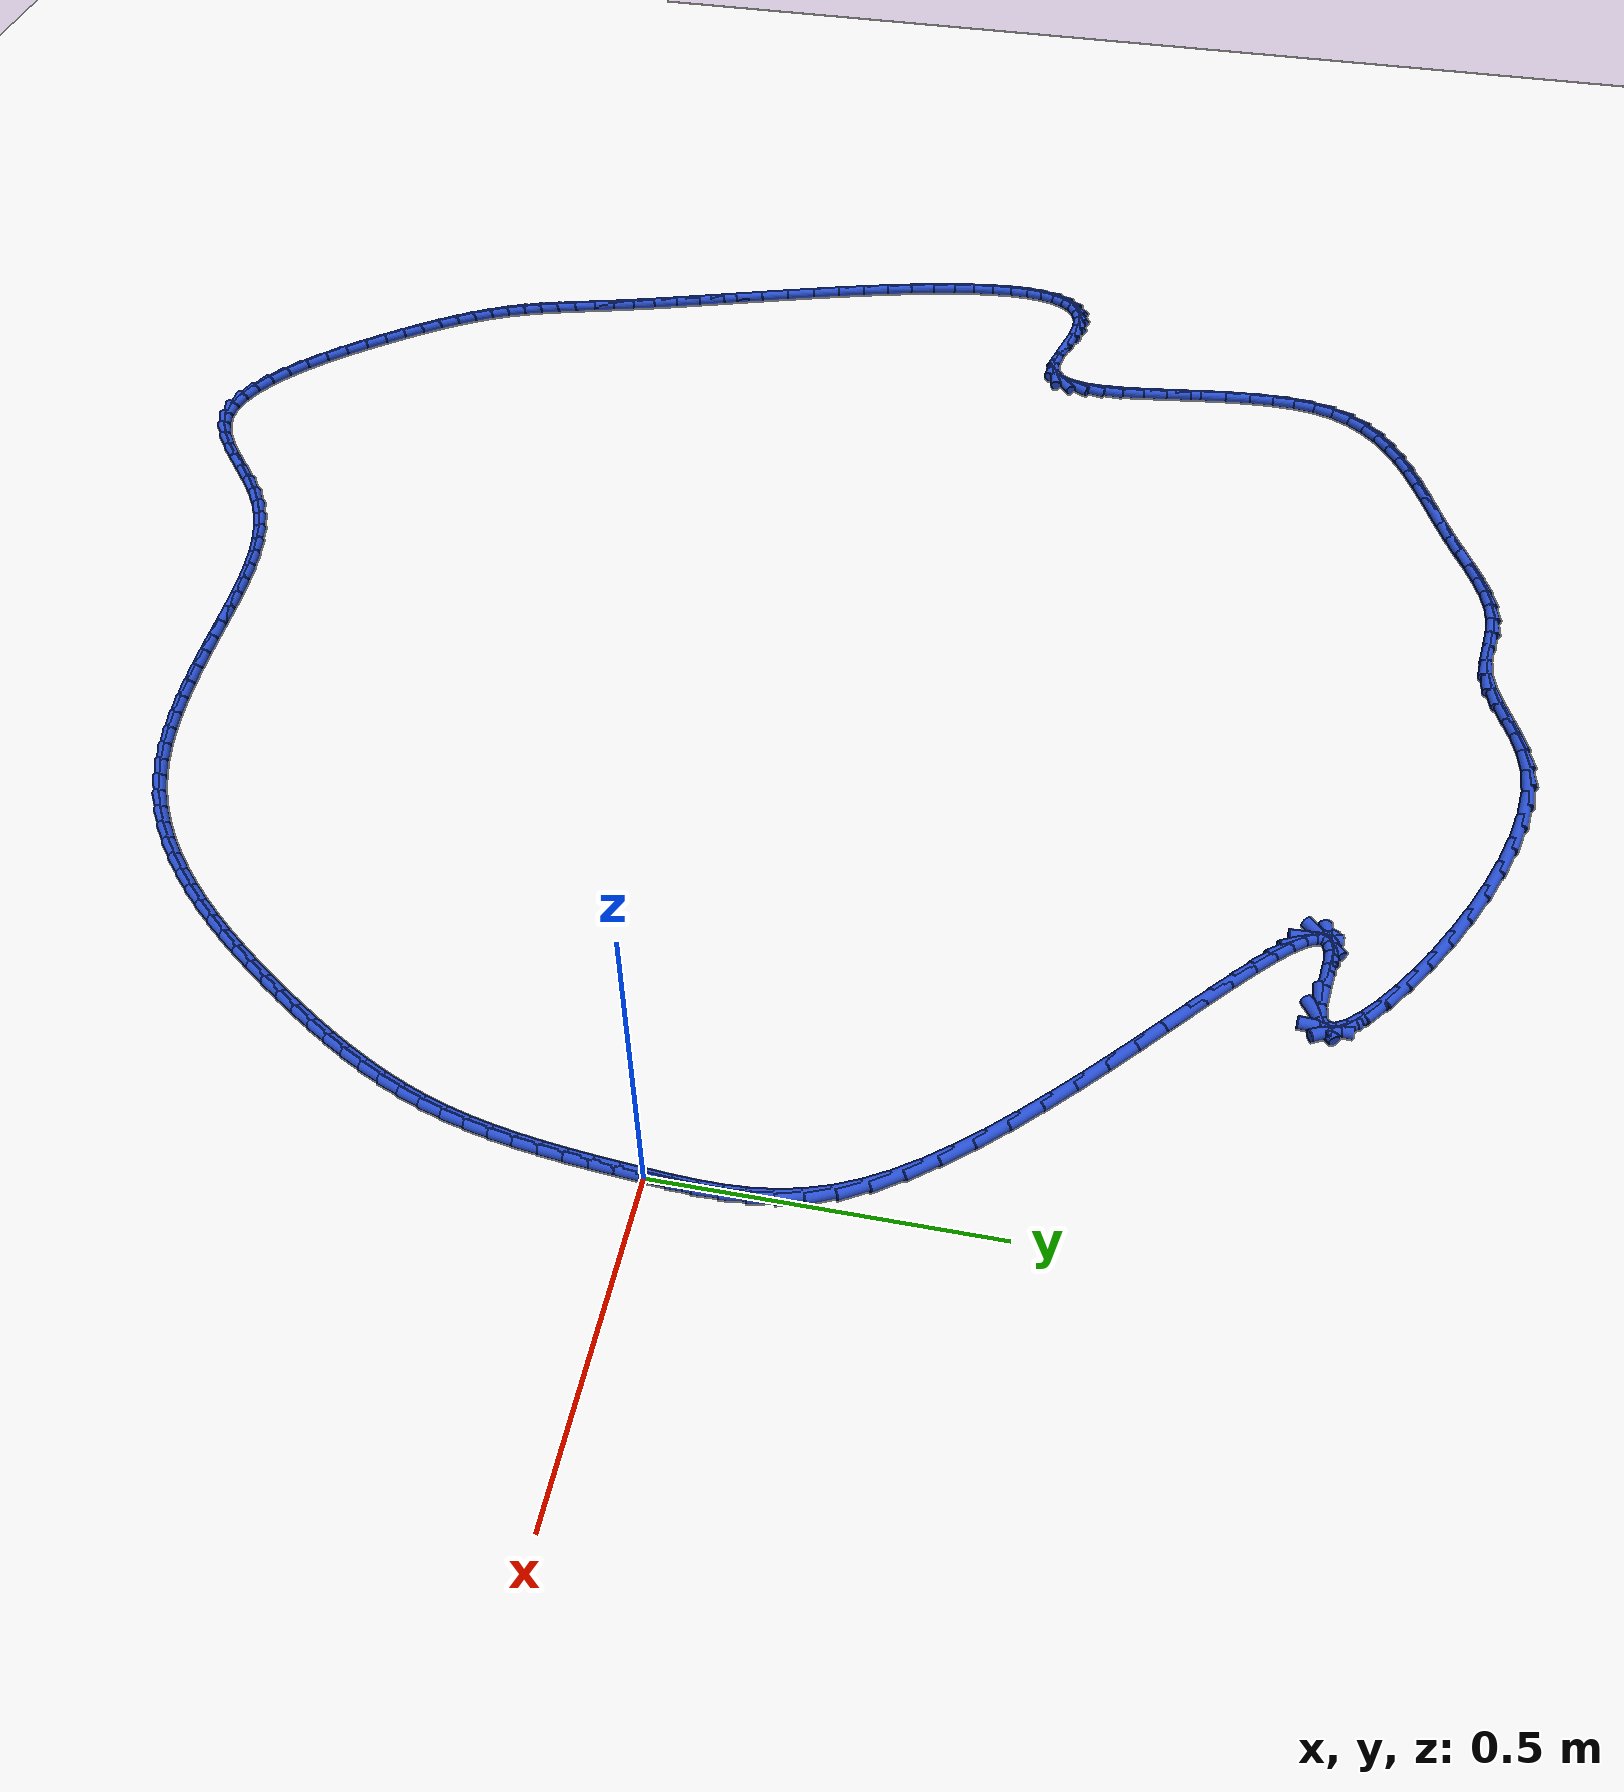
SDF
<sdf version="1.6">
 <world name="default">
  <light name="sun" type="directional">
   <pose>0 0 10 0 -0 0</pose>
   <diffuse>0.8 0.8 0.8 1</diffuse>
   <specular>0.2 0.2 0.2 1</specular>
   <attenuation>
    <range>1000</range>
    <constant>0.9</constant>
    <linear>0.01</linear>
    <quadratic>0.001</quadratic>
   </attenuation>
   <direction>-0.5 0.1 -0.9</direction>
  </light>
  <model name="ground_plane">
   <static>1</static>
   <link name="link">
    <collision name="collision">
     <geometry><plane><normal>0 0 1</normal><size>100 100</size></plane></geometry>
     <surface><friction><ode><mu>100</mu><mu2>50</mu2></ode></friction></surface>
    </collision>
    <visual name="visual">
     <cast_shadows>0</cast_shadows>
     <geometry><plane><normal>0 0 1</normal><size>100 100</size></plane></geometry>
     <material>
      <script><uri>file://media/materials/scripts/gazebo.material</uri><name>Gazebo/WhiteGlow</name></script>
     </material>
    </visual>
   </link>
  </model>
  <gravity>0 0 -9.8</gravity>
  <magnetic_field>6e-06 2.3e-05 -4.2e-05</magnetic_field>
  <atmosphere type="adiabatic"/>
  <physics name="default_physics" default="0" type="ode">
   <max_step_size>0.001</max_step_size>
   <real_time_factor>1</real_time_factor>
   <real_time_update_rate>1000</real_time_update_rate>
  </physics>
  <scene><ambient>0.4 0.4 0.4 1</ambient><background>0.7 0.7 0.7 1</background><shadows>1</shadows></scene>
  <spherical_coordinates>
   <surface_model>EARTH_WGS84</surface_model>
   <latitude_deg>0</latitude_deg>
   <longitude_deg>0</longitude_deg>
   <elevation>0</elevation>
   <heading_deg>0</heading_deg>
  </spherical_coordinates>
  <model name="line">
   <link name="link_0">
    <pose>2.8189256484623115e-17 4.85722573273506e-17 0.01 0 1.57 1.498070655885138</pose>
    <collision name="collision">
     <geometry><cylinder><radius>0.01</radius><length>0.08</length></cylinder></geometry>
    </collision>
    <visual name="visual">
     <material>
      <script><name>Gazebo/Blue</name><uri>file://media/materials/scripts/gazebo.material</uri></script>
     </material>
     <geometry><cylinder><radius>0.01</radius><length>0.08</length></cylinder></geometry>
    </visual>
   </link>
   <link name="link_1">
    <pose>0.002651591724945382 0.03639588698109935 0.01 0 1.57 1.521089725528869</pose>
    <collision name="collision">
     <geometry><cylinder><radius>0.01</radius><length>0.08</length></cylinder></geometry>
    </collision>
    <visual name="visual">
     <material>
      <script><name>Gazebo/Blue</name><uri>file://media/materials/scripts/gazebo.material</uri></script>
     </material>
     <geometry><cylinder><radius>0.01</radius><length>0.08</length></cylinder></geometry>
    </visual>
   </link>
   <link name="link_2">
    <pose>0.00444813783874525 0.07250912387801663 0.01 0 1.57 1.5635480753023947</pose>
    <collision name="collision">
     <geometry><cylinder><radius>0.01</radius><length>0.08</length></cylinder></geometry>
    </collision>
    <visual name="visual">
     <material>
      <script><name>Gazebo/Blue</name><uri>file://media/materials/scripts/gazebo.material</uri></script>
     </material>
     <geometry><cylinder><radius>0.01</radius><length>0.08</length></cylinder></geometry>
    </visual>
   </link>
   <link name="link_3">
    <pose>0.004709261461088529 0.10853423278882578 0.01 0 1.57 -1.516750078653827</pose>
    <collision name="collision">
     <geometry><cylinder><radius>0.01</radius><length>0.08</length></cylinder></geometry>
    </collision>
    <visual name="visual">
     <material>
      <script><name>Gazebo/Blue</name><uri>file://media/materials/scripts/gazebo.material</uri></script>
     </material>
     <geometry><cylinder><radius>0.01</radius><length>0.08</length></cylinder></geometry>
    </visual>
   </link>
   <link name="link_4">
    <pose>0.0027545857116641082 0.14466573581160083 0.01 0 1.57 -1.4384282908039918</pose>
    <collision name="collision">
     <geometry><cylinder><radius>0.01</radius><length>0.08</length></cylinder></geometry>
    </collision>
    <visual name="visual">
     <material>
      <script><name>Gazebo/Blue</name><uri>file://media/materials/scripts/gazebo.material</uri></script>
     </material>
     <geometry><cylinder><radius>0.01</radius><length>0.08</length></cylinder></geometry>
    </visual>
   </link>
   <link name="link_5">
    <pose>-0.0020962662898391174 0.1810981550444158 0.01 0 1.57 -1.3464261265264865</pose>
    <collision name="collision">
     <geometry><cylinder><radius>0.01</radius><length>0.08</length></cylinder></geometry>
    </collision>
    <visual name="visual">
     <material>
      <script><name>Gazebo/Blue</name><uri>file://media/materials/scripts/gazebo.material</uri></script>
     </material>
     <geometry><cylinder><radius>0.01</radius><length>0.08</length></cylinder></geometry>
    </visual>
   </link>
   <link name="link_6">
    <pose>-0.010523671423732239 0.21802601258534443 0.01 0 1.57 -1.2455792006755915</pose>
    <collision name="collision">
     <geometry><cylinder><radius>0.01</radius><length>0.08</length></cylinder></geometry>
    </collision>
    <visual name="visual">
     <material>
      <script><name>Gazebo/Blue</name><uri>file://media/materials/scripts/gazebo.material</uri></script>
     </material>
     <geometry><cylinder><radius>0.01</radius><length>0.08</length></cylinder></geometry>
    </visual>
   </link>
   <link name="link_7">
    <pose>-0.023208006570326407 0.2556438305324609 0.01 0 1.57 -1.1415760457312654</pose>
    <collision name="collision">
     <geometry><cylinder><radius>0.01</radius><length>0.08</length></cylinder></geometry>
    </collision>
    <visual name="visual">
     <material>
      <script><name>Gazebo/Blue</name><uri>file://media/materials/scripts/gazebo.material</uri></script>
     </material>
     <geometry><cylinder><radius>0.01</radius><length>0.08</length></cylinder></geometry>
    </visual>
   </link>
   <link name="link_8">
    <pose>-0.04082964860993267 0.29414613098383907 0.01 0 1.57 -1.0408057589957405</pose>
    <collision name="collision">
     <geometry><cylinder><radius>0.01</radius><length>0.08</length></cylinder></geometry>
    </collision>
    <visual name="visual">
     <material>
      <script><name>Gazebo/Blue</name><uri>file://media/materials/scripts/gazebo.material</uri></script>
     </material>
     <geometry><cylinder><radius>0.01</radius><length>0.08</length></cylinder></geometry>
    </visual>
   </link>
   <link name="link_9">
    <pose>-0.06400849119661083 0.3337069277028687 0.01 0 1.57 -0.9573538914795601</pose>
    <collision name="collision">
     <geometry><cylinder><radius>0.01</radius><length>0.08</length></cylinder></geometry>
    </collision>
    <visual name="visual">
     <material>
      <script><name>Gazebo/Blue</name><uri>file://media/materials/scripts/gazebo.material</uri></script>
     </material>
     <geometry><cylinder><radius>0.01</radius><length>0.08</length></cylinder></geometry>
    </visual>
   </link>
   <link name="link_10">
    <pose>-0.09253004297143363 0.374217315565136 0.01 0 1.57 -0.8941933568819888</pose>
    <collision name="collision">
     <geometry><cylinder><radius>0.01</radius><length>0.08</length></cylinder></geometry>
    </collision>
    <visual name="visual">
     <material>
      <script><name>Gazebo/Blue</name><uri>file://media/materials/scripts/gazebo.material</uri></script>
     </material>
     <geometry><cylinder><radius>0.01</radius><length>0.08</length></cylinder></geometry>
    </visual>
   </link>
   <link name="link_11">
    <pose>-0.12557180764105716 0.4153622303264594 0.01 0 1.57 -0.8458727699029034</pose>
    <collision name="collision">
     <geometry><cylinder><radius>0.01</radius><length>0.08</length></cylinder></geometry>
    </collision>
    <visual name="visual">
     <material>
      <script><name>Gazebo/Blue</name><uri>file://media/materials/scripts/gazebo.material</uri></script>
     </material>
     <geometry><cylinder><radius>0.01</radius><length>0.08</length></cylinder></geometry>
    </visual>
   </link>
   <link name="link_12">
    <pose>-0.16229750834467258 0.45682193510022123 0.01 0 1.57 -0.8086130680567273</pose>
    <collision name="collision">
     <geometry><cylinder><radius>0.01</radius><length>0.08</length></cylinder></geometry>
    </collision>
    <visual name="visual">
     <material>
      <script><name>Gazebo/Blue</name><uri>file://media/materials/scripts/gazebo.material</uri></script>
     </material>
     <geometry><cylinder><radius>0.01</radius><length>0.08</length></cylinder></geometry>
    </visual>
   </link>
   <link name="link_13">
    <pose>-0.2018708682214711 0.4982766929998031 0.01 0 1.57 -0.7799014036705338</pose>
    <collision name="collision">
     <geometry><cylinder><radius>0.01</radius><length>0.08</length></cylinder></geometry>
    </collision>
    <visual name="visual">
     <material>
      <script><name>Gazebo/Blue</name><uri>file://media/materials/scripts/gazebo.material</uri></script>
     </material>
     <geometry><cylinder><radius>0.01</radius><length>0.08</length></cylinder></geometry>
    </visual>
   </link>
   <link name="link_14">
    <pose>-0.24345561041064387 0.5394067671385868 0.01 0 1.57 -0.7580858329796094</pose>
    <collision name="collision">
     <geometry><cylinder><radius>0.01</radius><length>0.08</length></cylinder></geometry>
    </collision>
    <visual name="visual">
     <material>
      <script><name>Gazebo/Blue</name><uri>file://media/materials/scripts/gazebo.material</uri></script>
     </material>
     <geometry><cylinder><radius>0.01</radius><length>0.08</length></cylinder></geometry>
    </visual>
   </link>
   <link name="link_15">
    <pose>-0.2862154580513819 0.579892420629954 0.01 0 1.57 -0.7421284941975217</pose>
    <collision name="collision">
     <geometry><cylinder><radius>0.01</radius><length>0.08</length></cylinder></geometry>
    </collision>
    <visual name="visual">
     <material>
      <script><name>Gazebo/Blue</name><uri>file://media/materials/scripts/gazebo.material</uri></script>
     </material>
     <geometry><cylinder><radius>0.01</radius><length>0.08</length></cylinder></geometry>
    </visual>
   </link>
   <link name="link_16">
    <pose>-0.32931413428287637 0.619413916587287 0.01 0 1.57 -0.7314711626433812</pose>
    <collision name="collision">
     <geometry><cylinder><radius>0.01</radius><length>0.08</length></cylinder></geometry>
    </collision>
    <visual name="visual">
     <material>
      <script><name>Gazebo/Blue</name><uri>file://media/materials/scripts/gazebo.material</uri></script>
     </material>
     <geometry><cylinder><radius>0.01</radius><length>0.08</length></cylinder></geometry>
    </visual>
   </link>
   <link name="link_17">
    <pose>-0.3719153622443187 0.6576515181239674 0.01 0 1.57 -0.7259887604627213</pose>
    <collision name="collision">
     <geometry><cylinder><radius>0.01</radius><length>0.08</length></cylinder></geometry>
    </collision>
    <visual name="visual">
     <material>
      <script><name>Gazebo/Blue</name><uri>file://media/materials/scripts/gazebo.material</uri></script>
     </material>
     <geometry><cylinder><radius>0.01</radius><length>0.08</length></cylinder></geometry>
    </visual>
   </link>
   <link name="link_18">
    <pose>-0.4131828650748997 0.6942854883533769 0.01 0 1.57 -0.726031458598725</pose>
    <collision name="collision">
     <geometry><cylinder><radius>0.01</radius><length>0.08</length></cylinder></geometry>
    </collision>
    <visual name="visual">
     <material>
      <script><name>Gazebo/Blue</name><uri>file://media/materials/scripts/gazebo.material</uri></script>
     </material>
     <geometry><cylinder><radius>0.01</radius><length>0.08</length></cylinder></geometry>
    </visual>
   </link>
   <link name="link_19">
    <pose>-0.45228036591381066 0.7289960903888975 0.01 0 1.57 -0.7325915159307944</pose>
    <collision name="collision">
     <geometry><cylinder><radius>0.01</radius><length>0.08</length></cylinder></geometry>
    </collision>
    <visual name="visual">
     <material>
      <script><name>Gazebo/Blue</name><uri>file://media/materials/scripts/gazebo.material</uri></script>
     </material>
     <geometry><cylinder><radius>0.01</radius><length>0.08</length></cylinder></geometry>
    </visual>
   </link>
   <link name="link_20">
    <pose>-0.48837158790024293 0.7614635873439111 0.01 0 1.57 -0.7477026566951458</pose>
    <collision name="collision">
     <geometry><cylinder><radius>0.01</radius><length>0.08</length></cylinder></geometry>
    </collision>
    <visual name="visual">
     <material>
      <script><name>Gazebo/Blue</name><uri>file://media/materials/scripts/gazebo.material</uri></script>
     </material>
     <geometry><cylinder><radius>0.01</radius><length>0.08</length></cylinder></geometry>
    </visual>
   </link>
   <link name="link_21">
    <pose>-0.520620254173387 0.7913682423317991 0.01 0 1.57 -0.7753648235506219</pose>
    <collision name="collision">
     <geometry><cylinder><radius>0.01</radius><length>0.08</length></cylinder></geometry>
    </collision>
    <visual name="visual">
     <material>
      <script><name>Gazebo/Blue</name><uri>file://media/materials/scripts/gazebo.material</uri></script>
     </material>
     <geometry><cylinder><radius>0.01</radius><length>0.08</length></cylinder></geometry>
    </visual>
   </link>
   <link name="link_22">
    <pose>-0.5481900878724346 0.8183903184659436 0.01 0 1.57 -0.8238545287976053</pose>
    <collision name="collision">
     <geometry><cylinder><radius>0.01</radius><length>0.08</length></cylinder></geometry>
    </collision>
    <visual name="visual">
     <material>
      <script><name>Gazebo/Blue</name><uri>file://media/materials/scripts/gazebo.material</uri></script>
     </material>
     <geometry><cylinder><radius>0.01</radius><length>0.08</length></cylinder></geometry>
    </visual>
   </link>
   <link name="link_23">
    <pose>-0.5702448121365773 0.842210078859727 0.01 0 1.57 -0.9123297264157438</pose>
    <collision name="collision">
     <geometry><cylinder><radius>0.01</radius><length>0.08</length></cylinder></geometry>
    </collision>
    <visual name="visual">
     <material>
      <script><name>Gazebo/Blue</name><uri>file://media/materials/scripts/gazebo.material</uri></script>
     </material>
     <geometry><cylinder><radius>0.01</radius><length>0.08</length></cylinder></geometry>
    </visual>
   </link>
   <link name="link_24">
    <pose>-0.585948150105005 0.8625077866265303 0.01 0 1.57 -1.0932595328112906</pose>
    <collision name="collision">
     <geometry><cylinder><radius>0.01</radius><length>0.08</length></cylinder></geometry>
    </collision>
    <visual name="visual">
     <material>
      <script><name>Gazebo/Blue</name><uri>file://media/materials/scripts/gazebo.material</uri></script>
     </material>
     <geometry><cylinder><radius>0.01</radius><length>0.08</length></cylinder></geometry>
    </visual>
   </link>
   <link name="link_25">
    <pose>-0.59446382491691 0.8789637048797356 0.01 0 1.57 -1.530820959416895</pose>
    <collision name="collision">
     <geometry><cylinder><radius>0.01</radius><length>0.08</length></cylinder></geometry>
    </collision>
    <visual name="visual">
     <material>
      <script><name>Gazebo/Blue</name><uri>file://media/materials/scripts/gazebo.material</uri></script>
     </material>
     <geometry><cylinder><radius>0.01</radius><length>0.08</length></cylinder></geometry>
    </visual>
   </link>
   <link name="link_26">
    <pose>-0.5949555597114827 0.8912580967327247 0.01 0 1.57 0.7510915891292111</pose>
    <collision name="collision">
     <geometry><cylinder><radius>0.01</radius><length>0.08</length></cylinder></geometry>
    </collision>
    <visual name="visual">
     <material>
      <script><name>Gazebo/Blue</name><uri>file://media/materials/scripts/gazebo.material</uri></script>
     </material>
     <geometry><cylinder><radius>0.01</radius><length>0.08</length></cylinder></geometry>
    </visual>
   </link>
   <link name="link_27">
    <pose>-0.5865870776279147 0.8990712252988797 0.01 0 1.57 0.165218645053021</pose>
    <collision name="collision">
     <geometry><cylinder><radius>0.01</radius><length>0.08</length></cylinder></geometry>
    </collision>
    <visual name="visual">
     <material>
      <script><name>Gazebo/Blue</name><uri>file://media/materials/scripts/gazebo.material</uri></script>
     </material>
     <geometry><cylinder><radius>0.01</radius><length>0.08</length></cylinder></geometry>
    </visual>
   </link>
   <link name="link_28">
    <pose>-0.5685221018053971 0.9020833536915824 0.01 0 1.57 -0.07359959629239929</pose>
    <collision name="collision">
     <geometry><cylinder><radius>0.01</radius><length>0.08</length></cylinder></geometry>
    </collision>
    <visual name="visual">
     <material>
      <script><name>Gazebo/Blue</name><uri>file://media/materials/scripts/gazebo.material</uri></script>
     </material>
     <geometry><cylinder><radius>0.01</radius><length>0.08</length></cylinder></geometry>
    </visual>
   </link>
   <link name="link_29">
    <pose>-0.5399243954971938 0.8999747653389495 0.01 0 1.57 -0.1673033595862107</pose>
    <collision name="collision">
     <geometry><cylinder><radius>0.01</radius><length>0.08</length></cylinder></geometry>
    </collision>
    <visual name="visual">
     <material>
      <script><name>Gazebo/Blue</name><uri>file://media/materials/scripts/gazebo.material</uri></script>
     </material>
     <geometry><cylinder><radius>0.01</radius><length>0.08</length></cylinder></geometry>
    </visual>
   </link>
   <link name="link_30">
    <pose>-0.5023259296184317 0.8936250612204376 0.01 0 1.57 -0.14434320764437078</pose>
    <collision name="collision">
     <geometry><cylinder><radius>0.01</radius><length>0.08</length></cylinder></geometry>
    </collision>
    <visual name="visual">
     <material>
      <script><name>Gazebo/Blue</name><uri>file://media/materials/scripts/gazebo.material</uri></script>
     </material>
     <geometry><cylinder><radius>0.01</radius><length>0.08</length></cylinder></geometry>
    </visual>
   </link>
   <link name="link_31">
    <pose>-0.46601184879638075 0.8883466608693603 0.01 0 1.57 0.03879350655038756</pose>
    <collision name="collision">
     <geometry><cylinder><radius>0.01</radius><length>0.08</length></cylinder></geometry>
    </collision>
    <visual name="visual">
     <material>
      <script><name>Gazebo/Blue</name><uri>file://media/materials/scripts/gazebo.material</uri></script>
     </material>
     <geometry><cylinder><radius>0.01</radius><length>0.08</length></cylinder></geometry>
    </visual>
   </link>
   <link name="link_32">
    <pose>-0.4411278750823785 0.8893124820149695 0.01 0 1.57 0.5539418820419948</pose>
    <collision name="collision">
     <geometry><cylinder><radius>0.01</radius><length>0.08</length></cylinder></geometry>
    </collision>
    <visual name="visual">
     <material>
      <script><name>Gazebo/Blue</name><uri>file://media/materials/scripts/gazebo.material</uri></script>
     </material>
     <geometry><cylinder><radius>0.01</radius><length>0.08</length></cylinder></geometry>
    </visual>
   </link>
   <link name="link_33">
    <pose>-0.42888443552260574 0.8968855637131785 0.01 0 1.57 1.518120523577327</pose>
    <collision name="collision">
     <geometry><cylinder><radius>0.01</radius><length>0.08</length></cylinder></geometry>
    </collision>
    <visual name="visual">
     <material>
      <script><name>Gazebo/Blue</name><uri>file://media/materials/scripts/gazebo.material</uri></script>
     </material>
     <geometry><cylinder><radius>0.01</radius><length>0.08</length></cylinder></geometry>
    </visual>
   </link>
   <link name="link_34">
    <pose>-0.42818316919900706 0.9101861220371084 0.01 0 1.57 -1.0781198537421286</pose>
    <collision name="collision">
     <geometry><cylinder><radius>0.01</radius><length>0.08</length></cylinder></geometry>
    </collision>
    <visual name="visual">
     <material>
      <script><name>Gazebo/Blue</name><uri>file://media/materials/scripts/gazebo.material</uri></script>
     </material>
     <geometry><cylinder><radius>0.01</radius><length>0.08</length></cylinder></geometry>
    </visual>
   </link>
   <link name="link_35">
    <pose>-0.43792571221633325 0.9283343714572547 0.01 0 1.57 -0.8587580761709076</pose>
    <collision name="collision">
     <geometry><cylinder><radius>0.01</radius><length>0.08</length></cylinder></geometry>
    </collision>
    <visual name="visual">
     <material>
      <script><name>Gazebo/Blue</name><uri>file://media/materials/scripts/gazebo.material</uri></script>
     </material>
     <geometry><cylinder><radius>0.01</radius><length>0.08</length></cylinder></geometry>
    </visual>
   </link>
   <link name="link_36">
    <pose>-0.4570137006793342 0.9504505264441112 0.01 0 1.57 -0.744864199887757</pose>
    <collision name="collision">
     <geometry><cylinder><radius>0.01</radius><length>0.08</length></cylinder></geometry>
    </collision>
    <visual name="visual">
     <material>
      <script><name>Gazebo/Blue</name><uri>file://media/materials/scripts/gazebo.material</uri></script>
     </material>
     <geometry><cylinder><radius>0.01</radius><length>0.08</length></cylinder></geometry>
    </visual>
   </link>
   <link name="link_37">
    <pose>-0.484348770692761 0.9756548014681732 0.01 0 1.57 -0.6716491488227655</pose>
    <collision name="collision">
     <geometry><cylinder><radius>0.01</radius><length>0.08</length></cylinder></geometry>
    </collision>
    <visual name="visual">
     <material>
      <script><name>Gazebo/Blue</name><uri>file://media/materials/scripts/gazebo.material</uri></script>
     </material>
     <geometry><cylinder><radius>0.01</radius><length>0.08</length></cylinder></geometry>
    </visual>
   </link>
   <link name="link_38">
    <pose>-0.5188325583613634 1.003067410999935 0.01 0 1.57 -0.6167809873883432</pose>
    <collision name="collision">
     <geometry><cylinder><radius>0.01</radius><length>0.08</length></cylinder></geometry>
    </collision>
    <visual name="visual">
     <material>
      <script><name>Gazebo/Blue</name><uri>file://media/materials/scripts/gazebo.material</uri></script>
     </material>
     <geometry><cylinder><radius>0.01</radius><length>0.08</length></cylinder></geometry>
    </visual>
   </link>
   <link name="link_39">
    <pose>-0.5593666997898923 1.0318085695098913 0.01 0 1.57 -0.5705411907685887</pose>
    <collision name="collision">
     <geometry><cylinder><radius>0.01</radius><length>0.08</length></cylinder></geometry>
    </collision>
    <visual name="visual">
     <material>
      <script><name>Gazebo/Blue</name><uri>file://media/materials/scripts/gazebo.material</uri></script>
     </material>
     <geometry><cylinder><radius>0.01</radius><length>0.08</length></cylinder></geometry>
    </visual>
   </link>
   <link name="link_40">
    <pose>-0.6048528310830981 1.060998491468537 0.01 0 1.57 -0.5277322428226916</pose>
    <collision name="collision">
     <geometry><cylinder><radius>0.01</radius><length>0.08</length></cylinder></geometry>
    </collision>
    <visual name="visual">
     <material>
      <script><name>Gazebo/Blue</name><uri>file://media/materials/scripts/gazebo.material</uri></script>
     </material>
     <geometry><cylinder><radius>0.01</radius><length>0.08</length></cylinder></geometry>
    </visual>
   </link>
   <link name="link_41">
    <pose>-0.6541925883457309 1.0897573913463663 0.01 0 1.57 -0.48492368225102694</pose>
    <collision name="collision">
     <geometry><cylinder><radius>0.01</radius><length>0.08</length></cylinder></geometry>
    </collision>
    <visual name="visual">
     <material>
      <script><name>Gazebo/Blue</name><uri>file://media/materials/scripts/gazebo.material</uri></script>
     </material>
     <geometry><cylinder><radius>0.01</radius><length>0.08</length></cylinder></geometry>
    </visual>
   </link>
   <link name="link_42">
    <pose>-0.706287607682541 1.117205483613874 0.01 0 1.57 -0.4392709476307039</pose>
    <collision name="collision">
     <geometry><cylinder><radius>0.01</radius><length>0.08</length></cylinder></geometry>
    </collision>
    <visual name="visual">
     <material>
      <script><name>Gazebo/Blue</name><uri>file://media/materials/scripts/gazebo.material</uri></script>
     </material>
     <geometry><cylinder><radius>0.01</radius><length>0.08</length></cylinder></geometry>
    </visual>
   </link>
   <link name="link_43">
    <pose>-0.7600395251982793 1.142462982741555 0.01 0 1.57 -0.387832946035166</pose>
    <collision name="collision">
     <geometry><cylinder><radius>0.01</radius><length>0.08</length></cylinder></geometry>
    </collision>
    <visual name="visual">
     <material>
      <script><name>Gazebo/Blue</name><uri>file://media/materials/scripts/gazebo.material</uri></script>
     </material>
     <geometry><cylinder><radius>0.01</radius><length>0.08</length></cylinder></geometry>
    </visual>
   </link>
   <link name="link_44">
    <pose>-0.8143499769976962 1.164650103199904 0.01 0 1.57 -0.3269872247416956</pose>
    <collision name="collision">
     <geometry><cylinder><radius>0.01</radius><length>0.08</length></cylinder></geometry>
    </collision>
    <visual name="visual">
     <material>
      <script><name>Gazebo/Blue</name><uri>file://media/materials/scripts/gazebo.material</uri></script>
     </material>
     <geometry><cylinder><radius>0.01</radius><length>0.08</length></cylinder></geometry>
    </visual>
   </link>
   <link name="link_45">
    <pose>-0.8681205991855417 1.182887059459415 0.01 0 1.57 -0.251717407379841</pose>
    <collision name="collision">
     <geometry><cylinder><radius>0.01</radius><length>0.08</length></cylinder></geometry>
    </collision>
    <visual name="visual">
     <material>
      <script><name>Gazebo/Blue</name><uri>file://media/materials/scripts/gazebo.material</uri></script>
     </material>
     <geometry><cylinder><radius>0.01</radius><length>0.08</length></cylinder></geometry>
    </visual>
   </link>
   <link name="link_46">
    <pose>-0.9202530278665666 1.1962940659905832 0.01 0 1.57 -0.15458499880799778</pose>
    <collision name="collision">
     <geometry><cylinder><radius>0.01</radius><length>0.08</length></cylinder></geometry>
    </collision>
    <visual name="visual">
     <material>
      <script><name>Gazebo/Blue</name><uri>file://media/materials/scripts/gazebo.material</uri></script>
     </material>
     <geometry><cylinder><radius>0.01</radius><length>0.08</length></cylinder></geometry>
    </visual>
   </link>
   <link name="link_47">
    <pose>-0.9696488991455212 1.2039913372639033 0.01 0 1.57 -0.02451533468647624</pose>
    <collision name="collision">
     <geometry><cylinder><radius>0.01</radius><length>0.08</length></cylinder></geometry>
    </collision>
    <visual name="visual">
     <material>
      <script><name>Gazebo/Blue</name><uri>file://media/materials/scripts/gazebo.material</uri></script>
     </material>
     <geometry><cylinder><radius>0.01</radius><length>0.08</length></cylinder></geometry>
    </visual>
   </link>
   <link name="link_48">
    <pose>-1.0152164167254545 1.2051086640555857 0.01 0 1.57 0.128623617829759</pose>
    <collision name="collision">
     <geometry><cylinder><radius>0.01</radius><length>0.08</length></cylinder></geometry>
    </collision>
    <visual name="visual">
     <material>
      <script><name>Gazebo/Blue</name><uri>file://media/materials/scripts/gazebo.material</uri></script>
     </material>
     <geometry><cylinder><radius>0.01</radius><length>0.08</length></cylinder></geometry>
    </visual>
   </link>
   <link name="link_49">
    <pose>-1.0565413429474457 1.199763794742662 0.01 0 1.57 0.2542591177447824</pose>
    <collision name="collision">
     <geometry><cylinder><radius>0.01</radius><length>0.08</length></cylinder></geometry>
    </collision>
    <visual name="visual">
     <material>
      <script><name>Gazebo/Blue</name><uri>file://media/materials/scripts/gazebo.material</uri></script>
     </material>
     <geometry><cylinder><radius>0.01</radius><length>0.08</length></cylinder></geometry>
    </visual>
   </link>
   <link name="link_50">
    <pose>-1.0944666459044428 1.1899076267591426 0.01 0 1.57 0.3314110963329146</pose>
    <collision name="collision">
     <geometry><cylinder><radius>0.01</radius><length>0.08</length></cylinder></geometry>
    </collision>
    <visual name="visual">
     <material>
      <script><name>Gazebo/Blue</name><uri>file://media/materials/scripts/gazebo.material</uri></script>
     </material>
     <geometry><cylinder><radius>0.01</radius><length>0.08</length></cylinder></geometry>
    </visual>
   </link>
   <link name="link_51">
    <pose>-1.1299718682189255 1.1776901987453592 0.01 0 1.57 0.3498463522970453</pose>
    <collision name="collision">
     <geometry><cylinder><radius>0.01</radius><length>0.08</length></cylinder></geometry>
    </collision>
    <visual name="visual">
     <material>
      <script><name>Gazebo/Blue</name><uri>file://media/materials/scripts/gazebo.material</uri></script>
     </material>
     <geometry><cylinder><radius>0.01</radius><length>0.08</length></cylinder></geometry>
    </visual>
   </link>
   <link name="link_52">
    <pose>-1.1640365525133727 1.1652615493416412 0.01 0 1.57 0.30257792461313665</pose>
    <collision name="collision">
     <geometry><cylinder><radius>0.01</radius><length>0.08</length></cylinder></geometry>
    </collision>
    <visual name="visual">
     <material>
      <script><name>Gazebo/Blue</name><uri>file://media/materials/scripts/gazebo.material</uri></script>
     </material>
     <geometry><cylinder><radius>0.01</radius><length>0.08</length></cylinder></geometry>
    </visual>
   </link>
   <link name="link_53">
    <pose>-1.1976402414102638 1.1547717171883192 0.01 0 1.57 0.18543449530653613</pose>
    <collision name="collision">
     <geometry><cylinder><radius>0.01</radius><length>0.08</length></cylinder></geometry>
    </collision>
    <visual name="visual">
     <material>
      <script><name>Gazebo/Blue</name><uri>file://media/materials/scripts/gazebo.material</uri></script>
     </material>
     <geometry><cylinder><radius>0.01</radius><length>0.08</length></cylinder></geometry>
    </visual>
   </link>
   <link name="link_54">
    <pose>-1.2317624775320786 1.1483707409257244 0.01 0 1.57 0.008613292092740985</pose>
    <collision name="collision">
     <geometry><cylinder><radius>0.01</radius><length>0.08</length></cylinder></geometry>
    </collision>
    <visual name="visual">
     <material>
      <script><name>Gazebo/Blue</name><uri>file://media/materials/scripts/gazebo.material</uri></script>
     </material>
     <geometry><cylinder><radius>0.01</radius><length>0.08</length></cylinder></geometry>
    </visual>
   </link>
   <link name="link_55">
    <pose>-1.2673378902562373 1.1480643119267073 0.01 0 1.57 -0.1282680408193536</pose>
    <collision name="collision">
     <geometry><cylinder><radius>0.01</radius><length>0.08</length></cylinder></geometry>
    </collision>
    <visual name="visual">
     <material>
      <script><name>Gazebo/Blue</name><uri>file://media/materials/scripts/gazebo.material</uri></script>
     </material>
     <geometry><cylinder><radius>0.01</radius><length>0.08</length></cylinder></geometry>
    </visual>
   </link>
   <link name="link_56">
    <pose>-1.3043618807767237 1.1528395237843636 0.01 0 1.57 -0.1579123180442479</pose>
    <collision name="collision">
     <geometry><cylinder><radius>0.01</radius><length>0.08</length></cylinder></geometry>
    </collision>
    <visual name="visual">
     <material>
      <script><name>Gazebo/Blue</name><uri>file://media/materials/scripts/gazebo.material</uri></script>
     </material>
     <geometry><cylinder><radius>0.01</radius><length>0.08</length></cylinder></geometry>
    </visual>
   </link>
   <link name="link_57">
    <pose>-1.3419399425545793 1.1588233839548638 0.01 0 1.57 -0.08603056462603116</pose>
    <collision name="collision">
     <geometry><cylinder><radius>0.01</radius><length>0.08</length></cylinder></geometry>
    </collision>
    <visual name="visual">
     <material>
      <script><name>Gazebo/Blue</name><uri>file://media/materials/scripts/gazebo.material</uri></script>
     </material>
     <geometry><cylinder><radius>0.01</radius><length>0.08</length></cylinder></geometry>
    </visual>
   </link>
   <link name="link_58">
    <pose>-1.3791429454230293 1.1620318988882357 0.01 0 1.57 0.06459786658534925</pose>
    <collision name="collision">
     <geometry><cylinder><radius>0.01</radius><length>0.08</length></cylinder></geometry>
    </collision>
    <visual name="visual">
     <material>
      <script><name>Gazebo/Blue</name><uri>file://media/materials/scripts/gazebo.material</uri></script>
     </material>
     <geometry><cylinder><radius>0.01</radius><length>0.08</length></cylinder></geometry>
    </visual>
   </link>
   <link name="link_59">
    <pose>-1.4153534298748203 1.1596895197788168 0.01 0 1.57 0.2034330405025382</pose>
    <collision name="collision">
     <geometry><cylinder><radius>0.01</radius><length>0.08</length></cylinder></geometry>
    </collision>
    <visual name="visual">
     <material>
      <script><name>Gazebo/Blue</name><uri>file://media/materials/scripts/gazebo.material</uri></script>
     </material>
     <geometry><cylinder><radius>0.01</radius><length>0.08</length></cylinder></geometry>
    </visual>
   </link>
   <link name="link_60">
    <pose>-1.4508186635186442 1.1523735156323613 0.01 0 1.57 0.30707886094022574</pose>
    <collision name="collision">
     <geometry><cylinder><radius>0.01</radius><length>0.08</length></cylinder></geometry>
    </collision>
    <visual name="visual">
     <material>
      <script><name>Gazebo/Blue</name><uri>file://media/materials/scripts/gazebo.material</uri></script>
     </material>
     <geometry><cylinder><radius>0.01</radius><length>0.08</length></cylinder></geometry>
    </visual>
   </link>
   <link name="link_61">
    <pose>-1.4859346610823136 1.1412378946145003 0.01 0 1.57 0.3740202447851873</pose>
    <collision name="collision">
     <geometry><cylinder><radius>0.01</radius><length>0.08</length></cylinder></geometry>
    </collision>
    <visual name="visual">
     <material>
      <script><name>Gazebo/Blue</name><uri>file://media/materials/scripts/gazebo.material</uri></script>
     </material>
     <geometry><cylinder><radius>0.01</radius><length>0.08</length></cylinder></geometry>
    </visual>
   </link>
   <link name="link_62">
    <pose>-1.5210974372936383 1.1274366648908647 0.01 0 1.57 0.4061557813907793</pose>
    <collision name="collision">
     <geometry><cylinder><radius>0.01</radius><length>0.08</length></cylinder></geometry>
    </collision>
    <visual name="visual">
     <material>
      <script><name>Gazebo/Blue</name><uri>file://media/materials/scripts/gazebo.material</uri></script>
     </material>
     <geometry><cylinder><radius>0.01</radius><length>0.08</length></cylinder></geometry>
    </visual>
   </link>
   <link name="link_63">
    <pose>-1.5567030068804297 1.112123834627086 0.01 0 1.57 0.40608277976718715</pose>
    <collision name="collision">
     <geometry><cylinder><radius>0.01</radius><length>0.08</length></cylinder></geometry>
    </collision>
    <visual name="visual">
     <material>
      <script><name>Gazebo/Blue</name><uri>file://media/materials/scripts/gazebo.material</uri></script>
     </material>
     <geometry><cylinder><radius>0.01</radius><length>0.08</length></cylinder></geometry>
    </visual>
   </link>
   <link name="link_64">
    <pose>-1.5931473845704993 1.0964534119887959 0.01 0 1.57 0.38018506099345506</pose>
    <collision name="collision">
     <geometry><cylinder><radius>0.01</radius><length>0.08</length></cylinder></geometry>
    </collision>
    <visual name="visual">
     <material>
      <script><name>Gazebo/Blue</name><uri>file://media/materials/scripts/gazebo.material</uri></script>
     </material>
     <geometry><cylinder><radius>0.01</radius><length>0.08</length></cylinder></geometry>
    </visual>
   </link>
   <link name="link_65">
    <pose>-1.6307365694512521 1.081431746729248 0.01 0 1.57 0.3593951628032514</pose>
    <collision name="collision">
     <geometry><cylinder><radius>0.01</radius><length>0.08</length></cylinder></geometry>
    </collision>
    <visual name="visual">
     <material>
      <script><name>Gazebo/Blue</name><uri>file://media/materials/scripts/gazebo.material</uri></script>
     </material>
     <geometry><cylinder><radius>0.01</radius><length>0.08</length></cylinder></geometry>
    </visual>
   </link>
   <link name="link_66">
    <pose>-1.669131121927534 1.067006434248297 0.01 0 1.57 0.35595938100150765</pose>
    <collision name="collision">
     <geometry><cylinder><radius>0.01</radius><length>0.08</length></cylinder></geometry>
    </collision>
    <visual name="visual">
     <material>
      <script><name>Gazebo/Blue</name><uri>file://media/materials/scripts/gazebo.material</uri></script>
     </material>
     <geometry><cylinder><radius>0.01</radius><length>0.08</length></cylinder></geometry>
    </visual>
   </link>
   <link name="link_67">
    <pose>-1.7077098974092173 1.0526629712246305 0.01 0 1.57 0.36965076799145635</pose>
    <collision name="collision">
     <geometry><cylinder><radius>0.01</radius><length>0.08</length></cylinder></geometry>
    </collision>
    <visual name="visual">
     <material>
      <script><name>Gazebo/Blue</name><uri>file://media/materials/scripts/gazebo.material</uri></script>
     </material>
     <geometry><cylinder><radius>0.01</radius><length>0.08</length></cylinder></geometry>
    </visual>
   </link>
   <link name="link_68">
    <pose>-1.745850577147268 1.0378849282889833 0.01 0 1.57 0.4011837873824338</pose>
    <collision name="collision">
     <geometry><cylinder><radius>0.01</radius><length>0.08</length></cylinder></geometry>
    </collision>
    <visual name="visual">
     <material>
      <script><name>Gazebo/Blue</name><uri>file://media/materials/scripts/gazebo.material</uri></script>
     </material>
     <geometry><cylinder><radius>0.01</radius><length>0.08</length></cylinder></geometry>
    </visual>
   </link>
   <link name="link_69">
    <pose>-1.7829308423926526 1.0221558760720904 0.01 0 1.57 0.4522316653798287</pose>
    <collision name="collision">
     <geometry><cylinder><radius>0.01</radius><length>0.08</length></cylinder></geometry>
    </collision>
    <visual name="visual">
     <material>
      <script><name>Gazebo/Blue</name><uri>file://media/materials/scripts/gazebo.material</uri></script>
     </material>
     <geometry><cylinder><radius>0.01</radius><length>0.08</length></cylinder></geometry>
    </visual>
   </link>
   <link name="link_70">
    <pose>-1.8183283743963377 1.0049593852046865 0.01 0 1.57 0.5252834680330185</pose>
    <collision name="collision">
     <geometry><cylinder><radius>0.01</radius><length>0.08</length></cylinder></geometry>
    </collision>
    <visual name="visual">
     <material>
      <script><name>Gazebo/Blue</name><uri>file://media/materials/scripts/gazebo.material</uri></script>
     </material>
     <geometry><cylinder><radius>0.01</radius><length>0.08</length></cylinder></geometry>
    </visual>
   </link>
   <link name="link_71">
    <pose>-1.85142085440929 0.9857790263175079 0.01 0 1.57 0.6231880504689704</pose>
    <collision name="collision">
     <geometry><cylinder><radius>0.01</radius><length>0.08</length></cylinder></geometry>
    </collision>
    <visual name="visual">
     <material>
      <script><name>Gazebo/Blue</name><uri>file://media/materials/scripts/gazebo.material</uri></script>
     </material>
     <geometry><cylinder><radius>0.01</radius><length>0.08</length></cylinder></geometry>
    </visual>
   </link>
   <link name="link_72">
    <pose>-1.8815859636824757 0.9640983700412883 0.01 0 1.57 0.7480362558185244</pose>
    <collision name="collision">
     <geometry><cylinder><radius>0.01</radius><length>0.08</length></cylinder></geometry>
    </collision>
    <visual name="visual">
     <material>
      <script><name>Gazebo/Blue</name><uri>file://media/materials/scripts/gazebo.material</uri></script>
     </material>
     <geometry><cylinder><radius>0.01</radius><length>0.08</length></cylinder></geometry>
    </visual>
   </link>
   <link name="link_73">
    <pose>-1.9082013834668616 0.9394009870067631 0.01 0 1.57 0.899108724949676</pose>
    <collision name="collision">
     <geometry><cylinder><radius>0.01</radius><length>0.08</length></cylinder></geometry>
    </collision>
    <visual name="visual">
     <material>
      <script><name>Gazebo/Blue</name><uri>file://media/materials/scripts/gazebo.material</uri></script>
     </material>
     <geometry><cylinder><radius>0.01</radius><length>0.08</length></cylinder></geometry>
    </visual>
   </link>
   <link name="link_74">
    <pose>-1.9306447950134131 0.9111704478446672 0.01 0 1.57 1.070453496484405</pose>
    <collision name="collision">
     <geometry><cylinder><radius>0.01</radius><length>0.08</length></cylinder></geometry>
    </collision>
    <visual name="visual">
     <material>
      <script><name>Gazebo/Blue</name><uri>file://media/materials/scripts/gazebo.material</uri></script>
     </material>
     <geometry><cylinder><radius>0.01</radius><length>0.08</length></cylinder></geometry>
    </visual>
   </link>
   <link name="link_75">
    <pose>-1.9482938795730975 0.8788903231857358 0.01 0 1.57 1.2501654151754458</pose>
    <collision name="collision">
     <geometry><cylinder><radius>0.01</radius><length>0.08</length></cylinder></geometry>
    </collision>
    <visual name="visual">
     <material>
      <script><name>Gazebo/Blue</name><uri>file://media/materials/scripts/gazebo.material</uri></script>
     </material>
     <geometry><cylinder><radius>0.01</radius><length>0.08</length></cylinder></geometry>
    </visual>
   </link>
   <link name="link_76">
    <pose>-1.9605291811626064 0.8420469649930566 0.01 0 1.57 1.4108313898339337</pose>
    <collision name="collision">
     <geometry><cylinder><radius>0.01</radius><length>0.08</length></cylinder></geometry>
    </collision>
    <visual name="visual">
     <material>
      <script><name>Gazebo/Blue</name><uri>file://media/materials/scripts/gazebo.material</uri></script>
     </material>
     <geometry><cylinder><radius>0.01</radius><length>0.08</length></cylinder></geometry>
    </visual>
   </link>
   <link name="link_77">
    <pose>-1.967216649468028 0.8005983231954688 0.01 0 1.57 1.5257180630345022</pose>
    <collision name="collision">
     <geometry><cylinder><radius>0.01</radius><length>0.08</length></cylinder></geometry>
    </collision>
    <visual name="visual">
     <material>
      <script><name>Gazebo/Blue</name><uri>file://media/materials/scripts/gazebo.material</uri></script>
     </material>
     <geometry><cylinder><radius>0.01</radius><length>0.08</length></cylinder></geometry>
    </visual>
   </link>
   <link name="link_78">
    <pose>-1.9692509025557872 0.7555017549108624 0.01 0 1.57 -1.5373799631421574</pose>
    <collision name="collision">
     <geometry><cylinder><radius>0.01</radius><length>0.08</length></cylinder></geometry>
    </collision>
    <visual name="visual">
     <material>
      <script><name>Gazebo/Blue</name><uri>file://media/materials/scripts/gazebo.material</uri></script>
     </material>
     <geometry><cylinder><radius>0.01</radius><length>0.08</length></cylinder></geometry>
    </visual>
   </link>
   <link name="link_79">
    <pose>-1.9676576945604327 0.7078420230681055 0.01 0 1.57 -1.4856329678480424</pose>
    <collision name="collision">
     <geometry><cylinder><radius>0.01</radius><length>0.08</length></cylinder></geometry>
    </collision>
    <visual name="visual">
     <material>
      <script><name>Gazebo/Blue</name><uri>file://media/materials/scripts/gazebo.material</uri></script>
     </material>
     <geometry><cylinder><radius>0.01</radius><length>0.08</length></cylinder></geometry>
    </visual>
   </link>
   <link name="link_80">
    <pose>-1.9634627796165103 0.658703890596065 0.01 0 1.57 -1.454810834884861</pose>
    <collision name="collision">
     <geometry><cylinder><radius>0.01</radius><length>0.08</length></cylinder></geometry>
    </collision>
    <visual name="visual">
     <material>
      <script><name>Gazebo/Blue</name><uri>file://media/materials/scripts/gazebo.material</uri></script>
     </material>
     <geometry><cylinder><radius>0.01</radius><length>0.08</length></cylinder></geometry>
    </visual>
   </link>
   <link name="link_81">
    <pose>-1.9576919118585658 0.6091721204236084 0.01 0 1.57 -1.442089507361175</pose>
    <collision name="collision">
     <geometry><cylinder><radius>0.01</radius><length>0.08</length></cylinder></geometry>
    </collision>
    <visual name="visual">
     <material>
      <script><name>Gazebo/Blue</name><uri>file://media/materials/scripts/gazebo.material</uri></script>
     </material>
     <geometry><cylinder><radius>0.01</radius><length>0.08</length></cylinder></geometry>
    </visual>
   </link>
   <link name="link_82">
    <pose>-1.9513708454211478 0.560331475479603 0.01 0 1.57 -1.4472276751250552</pose>
    <collision name="collision">
     <geometry><cylinder><radius>0.01</radius><length>0.08</length></cylinder></geometry>
    </collision>
    <visual name="visual">
     <material>
      <script><name>Gazebo/Blue</name><uri>file://media/materials/scripts/gazebo.material</uri></script>
     </material>
     <geometry><cylinder><radius>0.01</radius><length>0.08</length></cylinder></geometry>
    </visual>
   </link>
   <link name="link_83">
    <pose>-1.945525334438802 0.5132667186929163 0.01 0 1.57 -1.472834923856593</pose>
    <collision name="collision">
     <geometry><cylinder><radius>0.01</radius><length>0.08</length></cylinder></geometry>
    </collision>
    <visual name="visual">
     <material>
      <script><name>Gazebo/Blue</name><uri>file://media/materials/scripts/gazebo.material</uri></script>
     </material>
     <geometry><cylinder><radius>0.01</radius><length>0.08</length></cylinder></geometry>
    </visual>
   </link>
   <link name="link_84">
    <pose>-1.9411811330460744 0.4690626129924157 0.01 0 1.57 -1.5256904111098226</pose>
    <collision name="collision">
     <geometry><cylinder><radius>0.01</radius><length>0.08</length></cylinder></geometry>
    </collision>
    <visual name="visual">
     <material>
      <script><name>Gazebo/Blue</name><uri>file://media/materials/scripts/gazebo.material</uri></script>
     </material>
     <geometry><cylinder><radius>0.01</radius><length>0.08</length></cylinder></geometry>
    </visual>
   </link>
   <link name="link_85">
    <pose>-1.939363995377513 0.42880392130696793 0.01 0 1.57 1.5215669505991989</pose>
    <collision name="collision">
     <geometry><cylinder><radius>0.01</radius><length>0.08</length></cylinder></geometry>
    </collision>
    <visual name="visual">
     <material>
      <script><name>Gazebo/Blue</name><uri>file://media/materials/scripts/gazebo.material</uri></script>
     </material>
     <geometry><cylinder><radius>0.01</radius><length>0.08</length></cylinder></geometry>
    </visual>
   </link>
   <link name="link_86">
    <pose>-1.9410996755676637 0.39357540656544066 0.01 0 1.57 1.3572206433870737</pose>
    <collision name="collision">
     <geometry><cylinder><radius>0.01</radius><length>0.08</length></cylinder></geometry>
    </collision>
    <visual name="visual">
     <material>
      <script><name>Gazebo/Blue</name><uri>file://media/materials/scripts/gazebo.material</uri></script>
     </material>
     <geometry><cylinder><radius>0.01</radius><length>0.08</length></cylinder></geometry>
    </visual>
   </link>
   <link name="link_87">
    <pose>-1.9474139277510742 0.36446183169670143 0.01 0 1.57 1.0726617431655097</pose>
    <collision name="collision">
     <geometry><cylinder><radius>0.01</radius><length>0.08</length></cylinder></geometry>
    </collision>
    <visual name="visual">
     <material>
      <script><name>Gazebo/Blue</name><uri>file://media/materials/scripts/gazebo.material</uri></script>
     </material>
     <geometry><cylinder><radius>0.01</radius><length>0.08</length></cylinder></geometry>
    </visual>
   </link>
   <link name="link_88">
    <pose>-1.9593325060622897 0.34254795962961737 0.01 0 1.57 0.6336967444818498</pose>
    <collision name="collision">
     <geometry><cylinder><radius>0.01</radius><length>0.08</length></cylinder></geometry>
    </collision>
    <visual name="visual">
     <material>
      <script><name>Gazebo/Blue</name><uri>file://media/materials/scripts/gazebo.material</uri></script>
     </material>
     <geometry><cylinder><radius>0.01</radius><length>0.08</length></cylinder></geometry>
    </visual>
   </link>
   <link name="link_89">
    <pose>-1.9778811646358583 0.32891855329305597 0.01 0 1.57 0.16119219974146323</pose>
    <collision name="collision">
     <geometry><cylinder><radius>0.01</radius><length>0.08</length></cylinder></geometry>
    </collision>
    <visual name="visual">
     <material>
      <script><name>Gazebo/Blue</name><uri>file://media/materials/scripts/gazebo.material</uri></script>
     </material>
     <geometry><cylinder><radius>0.01</radius><length>0.08</length></cylinder></geometry>
    </visual>
   </link>
   <link name="link_90">
    <pose>-2.004085099993887 0.32465771622533063 0.01 0 1.57 -0.14441951825249436</pose>
    <collision name="collision">
     <geometry><cylinder><radius>0.01</radius><length>0.08</length></cylinder></geometry>
    </collision>
    <visual name="visual">
     <material>
      <script><name>Gazebo/Blue</name><uri>file://media/materials/scripts/gazebo.material</uri></script>
     </material>
     <geometry><cylinder><radius>0.01</radius><length>0.08</length></cylinder></geometry>
    </visual>
   </link>
   <link name="link_91">
    <pose>-2.0378909882426184 0.3295741747965507 0.01 0 1.57 -0.2563564714336061</pose>
    <collision name="collision">
     <geometry><cylinder><radius>0.01</radius><length>0.08</length></cylinder></geometry>
    </collision>
    <visual name="visual">
     <material>
      <script><name>Gazebo/Blue</name><uri>file://media/materials/scripts/gazebo.material</uri></script>
     </material>
     <geometry><cylinder><radius>0.01</radius><length>0.08</length></cylinder></geometry>
    </visual>
   </link>
   <link name="link_92">
    <pose>-2.075918181503772 0.3395420121575911 0.01 0 1.57 -0.25920325822992685</pose>
    <collision name="collision">
     <geometry><cylinder><radius>0.01</radius><length>0.08</length></cylinder></geometry>
    </collision>
    <visual name="visual">
     <material>
      <script><name>Gazebo/Blue</name><uri>file://media/materials/scripts/gazebo.material</uri></script>
     </material>
     <geometry><cylinder><radius>0.01</radius><length>0.08</length></cylinder></geometry>
    </visual>
   </link>
   <link name="link_93">
    <pose>-2.1141464047635354 0.34967893649152515 0.01 0 1.57 -0.16135335954710123</pose>
    <collision name="collision">
     <geometry><cylinder><radius>0.01</radius><length>0.08</length></cylinder></geometry>
    </collision>
    <visual name="visual">
     <material>
      <script><name>Gazebo/Blue</name><uri>file://media/materials/scripts/gazebo.material</uri></script>
     </material>
     <geometry><cylinder><radius>0.01</radius><length>0.08</length></cylinder></geometry>
    </visual>
   </link>
   <link name="link_94">
    <pose>-2.1487223956959918 0.3553068141927821 0.01 0 1.57 0.02324669888049152</pose>
    <collision name="collision">
     <geometry><cylinder><radius>0.01</radius><length>0.08</length></cylinder></geometry>
    </collision>
    <visual name="visual">
     <material>
      <script><name>Gazebo/Blue</name><uri>file://media/materials/scripts/gazebo.material</uri></script>
     </material>
     <geometry><cylinder><radius>0.01</radius><length>0.08</length></cylinder></geometry>
    </visual>
   </link>
   <link name="link_95">
    <pose>-2.1781449656784413 0.3546227133322473 0.01 0 1.57 0.26589332979328667</pose>
    <collision name="collision">
     <geometry><cylinder><radius>0.01</radius><length>0.08</length></cylinder></geometry>
    </collision>
    <visual name="visual">
     <material>
      <script><name>Gazebo/Blue</name><uri>file://media/materials/scripts/gazebo.material</uri></script>
     </material>
     <geometry><cylinder><radius>0.01</radius><length>0.08</length></cylinder></geometry>
    </visual>
   </link>
   <link name="link_96">
    <pose>-2.2026512340393505 0.34794862941336613 0.01 0 1.57 0.5540584916845906</pose>
    <collision name="collision">
     <geometry><cylinder><radius>0.01</radius><length>0.08</length></cylinder></geometry>
    </collision>
    <visual name="visual">
     <material>
      <script><name>Gazebo/Blue</name><uri>file://media/materials/scripts/gazebo.material</uri></script>
     </material>
     <geometry><cylinder><radius>0.01</radius><length>0.08</length></cylinder></geometry>
    </visual>
   </link>
   <link name="link_97">
    <pose>-2.222519050326349 0.33565634702326347 0.01 0 1.57 0.8467954505629541</pose>
    <collision name="collision">
     <geometry><cylinder><radius>0.01</radius><length>0.08</length></cylinder></geometry>
    </collision>
    <visual name="visual">
     <material>
      <script><name>Gazebo/Blue</name><uri>file://media/materials/scripts/gazebo.material</uri></script>
     </material>
     <geometry><cylinder><radius>0.01</radius><length>0.08</length></cylinder></geometry>
    </visual>
   </link>
   <link name="link_98">
    <pose>-2.238026264087067 0.31811765074906445 0.01 0 1.57 1.0994050968879376</pose>
    <collision name="collision">
     <geometry><cylinder><radius>0.01</radius><length>0.08</length></cylinder></geometry>
    </collision>
    <visual name="visual">
     <material>
      <script><name>Gazebo/Blue</name><uri>file://media/materials/scripts/gazebo.material</uri></script>
     </material>
     <geometry><cylinder><radius>0.01</radius><length>0.08</length></cylinder></geometry>
    </visual>
   </link>
   <link name="link_99">
    <pose>-2.2494507248691376 0.2957043251778943 0.01 0 1.57 1.2949294324138876</pose>
    <collision name="collision">
     <geometry><cylinder><radius>0.01</radius><length>0.08</length></cylinder></geometry>
    </collision>
    <visual name="visual">
     <material>
      <script><name>Gazebo/Blue</name><uri>file://media/materials/scripts/gazebo.material</uri></script>
     </material>
     <geometry><cylinder><radius>0.01</radius><length>0.08</length></cylinder></geometry>
    </visual>
   </link>
   <link name="link_100">
    <pose>-2.2570702822201887 0.2687881548968778 0.01 0 1.57 1.4397364974301867</pose>
    <collision name="collision">
     <geometry><cylinder><radius>0.01</radius><length>0.08</length></cylinder></geometry>
    </collision>
    <visual name="visual">
     <material>
      <script><name>Gazebo/Blue</name><uri>file://media/materials/scripts/gazebo.material</uri></script>
     </material>
     <geometry><cylinder><radius>0.01</radius><length>0.08</length></cylinder></geometry>
    </visual>
   </link>
   <link name="link_101">
    <pose>-2.2611627856878527 0.23774092449314013 0.01 0 1.57 1.5465728616678007</pose>
    <collision name="collision">
     <geometry><cylinder><radius>0.01</radius><length>0.08</length></cylinder></geometry>
    </collision>
    <visual name="visual">
     <material>
      <script><name>Gazebo/Blue</name><uri>file://media/materials/scripts/gazebo.material</uri></script>
     </material>
     <geometry><cylinder><radius>0.01</radius><length>0.08</length></cylinder></geometry>
    </visual>
   </link>
   <link name="link_102">
    <pose>-2.2620060848197605 0.2029344185538063 0.01 0 1.57 -1.5151368562012628</pose>
    <collision name="collision">
     <geometry><cylinder><radius>0.01</radius><length>0.08</length></cylinder></geometry>
    </collision>
    <visual name="visual">
     <material>
      <script><name>Gazebo/Blue</name><uri>file://media/materials/scripts/gazebo.material</uri></script>
     </material>
     <geometry><cylinder><radius>0.01</radius><length>0.08</length></cylinder></geometry>
    </visual>
   </link>
   <link name="link_103">
    <pose>-2.259878029163542 0.16474042166600136 0.01 0 1.57 -1.4543252421018584</pose>
    <collision name="collision">
     <geometry><cylinder><radius>0.01</radius><length>0.08</length></cylinder></geometry>
    </collision>
    <visual name="visual">
     <material>
      <script><name>Gazebo/Blue</name><uri>file://media/materials/scripts/gazebo.material</uri></script>
     </material>
     <geometry><cylinder><radius>0.01</radius><length>0.08</length></cylinder></geometry>
    </visual>
   </link>
   <link name="link_104">
    <pose>-2.255056468266828 0.12353071841685026 0.01 0 1.57 -1.4072393299807355</pose>
    <collision name="collision">
     <geometry><cylinder><radius>0.01</radius><length>0.08</length></cylinder></geometry>
    </collision>
    <visual name="visual">
     <material>
      <script><name>Gazebo/Blue</name><uri>file://media/materials/scripts/gazebo.material</uri></script>
     </material>
     <geometry><cylinder><radius>0.01</radius><length>0.08</length></cylinder></geometry>
    </visual>
   </link>
   <link name="link_105">
    <pose>-2.247819251677251 0.07967709339347816 0.01 0 1.57 -1.3702785292008288</pose>
    <collision name="collision">
     <geometry><cylinder><radius>0.01</radius><length>0.08</length></cylinder></geometry>
    </collision>
    <visual name="visual">
     <material>
      <script><name>Gazebo/Blue</name><uri>file://media/materials/scripts/gazebo.material</uri></script>
     </material>
     <geometry><cylinder><radius>0.01</radius><length>0.08</length></cylinder></geometry>
    </visual>
   </link>
   <link name="link_106">
    <pose>-2.23844422894244 0.03355133118301013 0.01 0 1.57 -1.3409940630813981</pose>
    <collision name="collision">
     <geometry><cylinder><radius>0.01</radius><length>0.08</length></cylinder></geometry>
    </collision>
    <visual name="visual">
     <material>
      <script><name>Gazebo/Blue</name><uri>file://media/materials/scripts/gazebo.material</uri></script>
     </material>
     <geometry><cylinder><radius>0.01</radius><length>0.08</length></cylinder></geometry>
    </visual>
   </link>
   <link name="link_107">
    <pose>-2.2272092496100266 -0.014474783627428822 0.01 0 1.57 -1.3176975963674313</pose>
    <collision name="collision">
     <geometry><cylinder><radius>0.01</radius><length>0.08</length></cylinder></geometry>
    </collision>
    <visual name="visual">
     <material>
      <script><name>Gazebo/Blue</name><uri>file://media/materials/scripts/gazebo.material</uri></script>
     </material>
     <geometry><cylinder><radius>0.01</radius><length>0.08</length></cylinder></geometry>
    </visual>
   </link>
   <link name="link_108">
    <pose>-2.2143921632276404 -0.0640294664507137 0.01 0 1.57 -1.2992120448546616</pose>
    <collision name="collision">
     <geometry><cylinder><radius>0.01</radius><length>0.08</length></cylinder></geometry>
    </collision>
    <visual name="visual">
     <material>
      <script><name>Gazebo/Blue</name><uri>file://media/materials/scripts/gazebo.material</uri></script>
     </material>
     <geometry><cylinder><radius>0.01</radius><length>0.08</length></cylinder></geometry>
    </visual>
   </link>
   <link name="link_109">
    <pose>-2.200270819342913 -0.11474093269971938 0.01 0 1.57 -1.284713917359872</pose>
    <collision name="collision">
     <geometry><cylinder><radius>0.01</radius><length>0.08</length></cylinder></geometry>
    </collision>
    <visual name="visual">
     <material>
      <script><name>Gazebo/Blue</name><uri>file://media/materials/scripts/gazebo.material</uri></script>
     </material>
     <geometry><cylinder><radius>0.01</radius><length>0.08</length></cylinder></geometry>
    </visual>
   </link>
   <link name="link_110">
    <pose>-2.185123067503476 -0.16623739778732094 0.01 0 1.57 -1.2736336205190086</pose>
    <collision name="collision">
     <geometry><cylinder><radius>0.01</radius><length>0.08</length></cylinder></geometry>
    </collision>
    <visual name="visual">
     <material>
      <script><name>Gazebo/Blue</name><uri>file://media/materials/scripts/gazebo.material</uri></script>
     </material>
     <geometry><cylinder><radius>0.01</radius><length>0.08</length></cylinder></geometry>
    </visual>
   </link>
   <link name="link_111">
    <pose>-2.1692267572569595 -0.21814707712639322 0.01 0 1.57 -1.265593129409476</pose>
    <collision name="collision">
     <geometry><cylinder><radius>0.01</radius><length>0.08</length></cylinder></geometry>
    </collision>
    <visual name="visual">
     <material>
      <script><name>Gazebo/Blue</name><uri>file://media/materials/scripts/gazebo.material</uri></script>
     </material>
     <geometry><cylinder><radius>0.01</radius><length>0.08</length></cylinder></geometry>
    </visual>
   </link>
   <link name="link_112">
    <pose>-2.1528597381509935 -0.2700981861298112 0.01 0 1.57 -1.260368906387728</pose>
    <collision name="collision">
     <geometry><cylinder><radius>0.01</radius><length>0.08</length></cylinder></geometry>
    </collision>
    <visual name="visual">
     <material>
      <script><name>Gazebo/Blue</name><uri>file://media/materials/scripts/gazebo.material</uri></script>
     </material>
     <geometry><cylinder><radius>0.01</radius><length>0.08</length></cylinder></geometry>
    </visual>
   </link>
   <link name="link_113">
    <pose>-2.1362998597332092 -0.3217189402104498 0.01 0 1.57 -1.2578734315430702</pose>
    <collision name="collision">
     <geometry><cylinder><radius>0.01</radius><length>0.08</length></cylinder></geometry>
    </collision>
    <visual name="visual">
     <material>
      <script><name>Gazebo/Blue</name><uri>file://media/materials/scripts/gazebo.material</uri></script>
     </material>
     <geometry><cylinder><radius>0.01</radius><length>0.08</length></cylinder></geometry>
    </visual>
   </link>
   <link name="link_114">
    <pose>-2.119824971551238 -0.3726375547811841 0.01 0 1.57 -1.258152557251033</pose>
    <collision name="collision">
     <geometry><cylinder><radius>0.01</radius><length>0.08</length></cylinder></geometry>
    </collision>
    <visual name="visual">
     <material>
      <script><name>Gazebo/Blue</name><uri>file://media/materials/scripts/gazebo.material</uri></script>
     </material>
     <geometry><cylinder><radius>0.01</radius><length>0.08</length></cylinder></geometry>
    </visual>
   </link>
   <link name="link_115">
    <pose>-2.10371292315271 -0.42248224525488887 0.01 0 1.57 -1.261399195949781</pose>
    <collision name="collision">
     <geometry><cylinder><radius>0.01</radius><length>0.08</length></cylinder></geometry>
    </collision>
    <visual name="visual">
     <material>
      <script><name>Gazebo/Blue</name><uri>file://media/materials/scripts/gazebo.material</uri></script>
     </material>
     <geometry><cylinder><radius>0.01</radius><length>0.08</length></cylinder></geometry>
    </visual>
   </link>
   <link name="link_116">
    <pose>-2.0882415640852576 -0.4708812270444383 0.01 0 1.57 -1.2679876373898318</pose>
    <collision name="collision">
     <geometry><cylinder><radius>0.01</radius><length>0.08</length></cylinder></geometry>
    </collision>
    <visual name="visual">
     <material>
      <script><name>Gazebo/Blue</name><uri>file://media/materials/scripts/gazebo.material</uri></script>
     </material>
     <geometry><cylinder><radius>0.01</radius><length>0.08</length></cylinder></geometry>
    </visual>
   </link>
   <link name="link_117">
    <pose>-2.0736887438965086 -0.5174627155627091 0.01 0 1.57 -1.2785385148607329</pose>
    <collision name="collision">
     <geometry><cylinder><radius>0.01</radius><length>0.08</length></cylinder></geometry>
    </collision>
    <visual name="visual">
     <material>
      <script><name>Gazebo/Blue</name><uri>file://media/materials/scripts/gazebo.material</uri></script>
     </material>
     <geometry><cylinder><radius>0.01</radius><length>0.08</length></cylinder></geometry>
    </visual>
   </link>
   <link name="link_118">
    <pose>-2.060332312134096 -0.5618549262225755 0.01 0 1.57 -1.293382688878935</pose>
    <collision name="collision">
     <geometry><cylinder><radius>0.01</radius><length>0.08</length></cylinder></geometry>
    </collision>
    <visual name="visual">
     <material>
      <script><name>Gazebo/Blue</name><uri>file://media/materials/scripts/gazebo.material</uri></script>
     </material>
     <geometry><cylinder><radius>0.01</radius><length>0.08</length></cylinder></geometry>
    </visual>
   </link>
   <link name="link_119">
    <pose>-2.0484116001520745 -0.6037178000603545 0.01 0 1.57 -1.3050261008933317</pose>
    <collision name="collision">
     <geometry><cylinder><radius>0.01</radius><length>0.08</length></cylinder></geometry>
    </collision>
    <visual name="visual">
     <material>
      <script><name>Gazebo/Blue</name><uri>file://media/materials/scripts/gazebo.material</uri></script>
     </material>
     <geometry><cylinder><radius>0.01</radius><length>0.08</length></cylinder></geometry>
    </visual>
   </link>
   <link name="link_120">
    <pose>-2.037690630840945 -0.6431027673265324 0.01 0 1.57 -1.3063974176832231</pose>
    <collision name="collision">
     <geometry><cylinder><radius>0.01</radius><length>0.08</length></cylinder></geometry>
    </collision>
    <visual name="visual">
     <material>
      <script><name>Gazebo/Blue</name><uri>file://media/materials/scripts/gazebo.material</uri></script>
     </material>
     <geometry><cylinder><radius>0.01</radius><length>0.08</length></cylinder></geometry>
    </visual>
   </link>
   <link name="link_121">
    <pose>-2.027613174560889 -0.68032503521024 0.01 0 1.57 -1.2954345021038127</pose>
    <collision name="collision">
     <geometry><cylinder><radius>0.01</radius><length>0.08</length></cylinder></geometry>
    </collision>
    <visual name="visual">
     <material>
      <script><name>Gazebo/Blue</name><uri>file://media/materials/scripts/gazebo.material</uri></script>
     </material>
     <geometry><cylinder><radius>0.01</radius><length>0.08</length></cylinder></geometry>
    </visual>
   </link>
   <link name="link_122">
    <pose>-2.0176170183600117 -0.7157047390732031 0.01 0 1.57 -1.2706942588044625</pose>
    <collision name="collision">
     <geometry><cylinder><radius>0.01</radius><length>0.08</length></cylinder></geometry>
    </collision>
    <visual name="visual">
     <material>
      <script><name>Gazebo/Blue</name><uri>file://media/materials/scripts/gazebo.material</uri></script>
     </material>
     <geometry><cylinder><radius>0.01</radius><length>0.08</length></cylinder></geometry>
    </visual>
   </link>
   <link name="link_123">
    <pose>-2.0071399492864157 -0.749562014277146 0.01 0 1.57 -1.2316424025399422</pose>
    <collision name="collision">
     <geometry><cylinder><radius>0.01</radius><length>0.08</length></cylinder></geometry>
    </collision>
    <visual name="visual">
     <material>
      <script><name>Gazebo/Blue</name><uri>file://media/materials/scripts/gazebo.material</uri></script>
     </material>
     <geometry><cylinder><radius>0.01</radius><length>0.08</length></cylinder></geometry>
    </visual>
   </link>
   <link name="link_124">
    <pose>-1.9956197543882053 -0.7822169961837941 0.01 0 1.57 -1.1790432622625637</pose>
    <collision name="collision">
     <geometry><cylinder><radius>0.01</radius><length>0.08</length></cylinder></geometry>
    </collision>
    <visual name="visual">
     <material>
      <script><name>Gazebo/Blue</name><uri>file://media/materials/scripts/gazebo.material</uri></script>
     </material>
     <geometry><cylinder><radius>0.01</radius><length>0.08</length></cylinder></geometry>
    </visual>
   </link>
   <link name="link_125">
    <pose>-1.9824942207134857 -0.8139898201548731 0.01 0 1.57 -1.1176728468232866</pose>
    <collision name="collision">
     <geometry><cylinder><radius>0.01</radius><length>0.08</length></cylinder></geometry>
    </collision>
    <visual name="visual">
     <material>
      <script><name>Gazebo/Blue</name><uri>file://media/materials/scripts/gazebo.material</uri></script>
     </material>
     <geometry><cylinder><radius>0.01</radius><length>0.08</length></cylinder></geometry>
    </visual>
   </link>
   <link name="link_126">
    <pose>-1.9673078032241575 -0.8451789867155206 0.01 0 1.57 -1.0599376970587293</pose>
    <collision name="collision">
     <geometry><cylinder><radius>0.01</radius><length>0.08</length></cylinder></geometry>
    </collision>
    <visual name="visual">
     <material>
      <script><name>Gazebo/Blue</name><uri>file://media/materials/scripts/gazebo.material</uri></script>
     </material>
     <geometry><cylinder><radius>0.01</radius><length>0.08</length></cylinder></geometry>
    </visual>
   </link>
   <link name="link_127">
    <pose>-1.9500354617529867 -0.8759956795755426 0.01 0 1.57 -1.0091780114156697</pose>
    <collision name="collision">
     <geometry><cylinder><radius>0.01</radius><length>0.08</length></cylinder></geometry>
    </collision>
    <visual name="visual">
     <material>
      <script><name>Gazebo/Blue</name><uri>file://media/materials/scripts/gazebo.material</uri></script>
     </material>
     <geometry><cylinder><radius>0.01</radius><length>0.08</length></cylinder></geometry>
    </visual>
   </link>
   <link name="link_128">
    <pose>-1.9307607492480536 -0.9066290571306587 0.01 0 1.57 -0.9656541544773847</pose>
    <collision name="collision">
     <geometry><cylinder><radius>0.01</radius><length>0.08</length></cylinder></geometry>
    </collision>
    <visual name="visual">
     <material>
      <script><name>Gazebo/Blue</name><uri>file://media/materials/scripts/gazebo.material</uri></script>
     </material>
     <geometry><cylinder><radius>0.01</radius><length>0.08</length></cylinder></geometry>
    </visual>
   </link>
   <link name="link_129">
    <pose>-1.9095672186602908 -0.9372682777760102 0.01 0 1.57 -0.9293089192465123</pose>
    <collision name="collision">
     <geometry><cylinder><radius>0.01</radius><length>0.08</length></cylinder></geometry>
    </collision>
    <visual name="visual">
     <material>
      <script><name>Gazebo/Blue</name><uri>file://media/materials/scripts/gazebo.material</uri></script>
     </material>
     <geometry><cylinder><radius>0.01</radius><length>0.08</length></cylinder></geometry>
    </visual>
   </link>
   <link name="link_130">
    <pose>-1.886538422940629 -0.9681024999067379 0.01 0 1.57 -0.8998599724028115</pose>
    <collision name="collision">
     <geometry><cylinder><radius>0.01</radius><length>0.08</length></cylinder></geometry>
    </collision>
    <visual name="visual">
     <material>
      <script><name>Gazebo/Blue</name><uri>file://media/materials/scripts/gazebo.material</uri></script>
     </material>
     <geometry><cylinder><radius>0.01</radius><length>0.08</length></cylinder></geometry>
    </visual>
   </link>
   <link name="link_131">
    <pose>-1.8617579150400012 -0.9993208819179836 0.01 0 1.57 -0.8768609260370717</pose>
    <collision name="collision">
     <geometry><cylinder><radius>0.01</radius><length>0.08</length></cylinder></geometry>
    </collision>
    <visual name="visual">
     <material>
      <script><name>Gazebo/Blue</name><uri>file://media/materials/scripts/gazebo.material</uri></script>
     </material>
     <geometry><cylinder><radius>0.01</radius><length>0.08</length></cylinder></geometry>
    </visual>
   </link>
   <link name="link_132">
    <pose>-1.835309484121929 -1.0311108618993503 0.01 0 1.57 -0.855945423599159</pose>
    <collision name="collision">
     <geometry><cylinder><radius>0.01</radius><length>0.08</length></cylinder></geometry>
    </collision>
    <visual name="visual">
     <material>
      <script><name>Gazebo/Blue</name><uri>file://media/materials/scripts/gazebo.material</uri></script>
     </material>
     <geometry><cylinder><radius>0.01</radius><length>0.08</length></cylinder></geometry>
    </visual>
   </link>
   <link name="link_133">
    <pose>-1.8073182497026599 -1.063358874362462 0.01 0 1.57 -0.8282817060563982</pose>
    <collision name="collision">
     <geometry><cylinder><radius>0.01</radius><length>0.08</length></cylinder></geometry>
    </collision>
    <visual name="visual">
     <material>
      <script><name>Gazebo/Blue</name><uri>file://media/materials/scripts/gazebo.material</uri></script>
     </material>
     <geometry><cylinder><radius>0.01</radius><length>0.08</length></cylinder></geometry>
    </visual>
   </link>
   <link name="link_134">
    <pose>-1.7779975800598566 -1.0953086495789075 0.01 0 1.57 -0.7917213569577052</pose>
    <collision name="collision">
     <geometry><cylinder><radius>0.01</radius><length>0.08</length></cylinder></geometry>
    </collision>
    <visual name="visual">
     <material>
      <script><name>Gazebo/Blue</name><uri>file://media/materials/scripts/gazebo.material</uri></script>
     </material>
     <geometry><cylinder><radius>0.01</radius><length>0.08</length></cylinder></geometry>
    </visual>
   </link>
   <link name="link_135">
    <pose>-1.7475721928658803 -1.1261212616563088 0.01 0 1.57 -0.7443705569233865</pose>
    <collision name="collision">
     <geometry><cylinder><radius>0.01</radius><length>0.08</length></cylinder></geometry>
    </collision>
    <visual name="visual">
     <material>
      <script><name>Gazebo/Blue</name><uri>file://media/materials/scripts/gazebo.material</uri></script>
     </material>
     <geometry><cylinder><radius>0.01</radius><length>0.08</length></cylinder></geometry>
    </visual>
   </link>
   <link name="link_136">
    <pose>-1.7162668057930908 -1.1549577847022878 0.01 0 1.57 -0.6833233561688374</pose>
    <collision name="collision">
     <geometry><cylinder><radius>0.01</radius><length>0.08</length></cylinder></geometry>
    </collision>
    <visual name="visual">
     <material>
      <script><name>Gazebo/Blue</name><uri>file://media/materials/scripts/gazebo.material</uri></script>
     </material>
     <geometry><cylinder><radius>0.01</radius><length>0.08</length></cylinder></geometry>
    </visual>
   </link>
   <link name="link_137">
    <pose>-1.684306136513849 -1.1809792928244687 0.01 0 1.57 -0.6043513217411646</pose>
    <collision name="collision">
     <geometry><cylinder><radius>0.01</radius><length>0.08</length></cylinder></geometry>
    </collision>
    <visual name="visual">
     <material>
      <script><name>Gazebo/Blue</name><uri>file://media/materials/scripts/gazebo.material</uri></script>
     </material>
     <geometry><cylinder><radius>0.01</radius><length>0.08</length></cylinder></geometry>
    </visual>
   </link>
   <link name="link_138">
    <pose>-1.6519149027005147 -1.2033468601304715 0.01 0 1.57 -0.5015776896897324</pose>
    <collision name="collision">
     <geometry><cylinder><radius>0.01</radius><length>0.08</length></cylinder></geometry>
    </collision>
    <visual name="visual">
     <material>
      <script><name>Gazebo/Blue</name><uri>file://media/materials/scripts/gazebo.material</uri></script>
     </material>
     <geometry><cylinder><radius>0.01</radius><length>0.08</length></cylinder></geometry>
    </visual>
   </link>
   <link name="link_139">
    <pose>-1.6193178220254494 -1.2212215607279207 0.01 0 1.57 -0.3675167871346827</pose>
    <collision name="collision">
     <geometry><cylinder><radius>0.01</radius><length>0.08</length></cylinder></geometry>
    </collision>
    <visual name="visual">
     <material>
      <script><name>Gazebo/Blue</name><uri>file://media/materials/scripts/gazebo.material</uri></script>
     </material>
     <geometry><cylinder><radius>0.01</radius><length>0.08</length></cylinder></geometry>
    </visual>
   </link>
   <link name="link_140">
    <pose>-1.5867396121610127 -1.233764468724438 0.01 0 1.57 -0.19457684001032965</pose>
    <collision name="collision">
     <geometry><cylinder><radius>0.01</radius><length>0.08</length></cylinder></geometry>
    </collision>
    <visual name="visual">
     <material>
      <script><name>Gazebo/Blue</name><uri>file://media/materials/scripts/gazebo.material</uri></script>
     </material>
     <geometry><cylinder><radius>0.01</radius><length>0.08</length></cylinder></geometry>
    </visual>
   </link>
   <link name="link_141">
    <pose>-1.5544049907795658 -1.2401366582276452 0.01 0 1.57 0.020001367277138707</pose>
    <collision name="collision">
     <geometry><cylinder><radius>0.01</radius><length>0.08</length></cylinder></geometry>
    </collision>
    <visual name="visual">
     <material>
      <script><name>Gazebo/Blue</name><uri>file://media/materials/scripts/gazebo.material</uri></script>
     </material>
     <geometry><cylinder><radius>0.01</radius><length>0.08</length></cylinder></geometry>
    </visual>
   </link>
   <link name="link_142">
    <pose>-1.5225386755534678 -1.239499203345166 0.01 0 1.57 0.2596052485259857</pose>
    <collision name="collision">
     <geometry><cylinder><radius>0.01</radius><length>0.08</length></cylinder></geometry>
    </collision>
    <visual name="visual">
     <material>
      <script><name>Gazebo/Blue</name><uri>file://media/materials/scripts/gazebo.material</uri></script>
     </material>
     <geometry><cylinder><radius>0.01</radius><length>0.08</length></cylinder></geometry>
    </visual>
   </link>
   <link name="link_143">
    <pose>-1.4913276174668915 -1.231209580679073 0.01 0 1.57 0.45589048234199414</pose>
    <collision name="collision">
     <geometry><cylinder><radius>0.01</radius><length>0.08</length></cylinder></geometry>
    </collision>
    <visual name="visual">
     <material>
      <script><name>Gazebo/Blue</name><uri>file://media/materials/scripts/gazebo.material</uri></script>
     </material>
     <geometry><cylinder><radius>0.01</radius><length>0.08</length></cylinder></geometry>
    </visual>
   </link>
   <link name="link_144">
    <pose>-1.460661227862808 -1.2161725967810153 0.01 0 1.57 0.5856708021701796</pose>
    <collision name="collision">
     <geometry><cylinder><radius>0.01</radius><length>0.08</length></cylinder></geometry>
    </collision>
    <visual name="visual">
     <material>
      <script><name>Gazebo/Blue</name><uri>file://media/materials/scripts/gazebo.material</uri></script>
     </material>
     <geometry><cylinder><radius>0.01</radius><length>0.08</length></cylinder></geometry>
    </visual>
   </link>
   <link name="link_145">
    <pose>-1.4302879947914167 -1.1960259179675319 0.01 0 1.57 0.6615036831508295</pose>
    <collision name="collision">
     <geometry><cylinder><radius>0.01</radius><length>0.08</length></cylinder></geometry>
    </collision>
    <visual name="visual">
     <material>
      <script><name>Gazebo/Blue</name><uri>file://media/materials/scripts/gazebo.material</uri></script>
     </material>
     <geometry><cylinder><radius>0.01</radius><length>0.08</length></cylinder></geometry>
    </visual>
   </link>
   <link name="link_146">
    <pose>-1.399955562356318 -1.1724115994286834 0.01 0 1.57 0.6944789218942741</pose>
    <collision name="collision">
     <geometry><cylinder><radius>0.01</radius><length>0.08</length></cylinder></geometry>
    </collision>
    <visual name="visual">
     <material>
      <script><name>Gazebo/Blue</name><uri>file://media/materials/scripts/gazebo.material</uri></script>
     </material>
     <geometry><cylinder><radius>0.01</radius><length>0.08</length></cylinder></geometry>
    </visual>
   </link>
   <link name="link_147">
    <pose>-1.3694115746611093 -1.146971696354529 0.01 0 1.57 0.690603843079649</pose>
    <collision name="collision">
     <geometry><cylinder><radius>0.01</radius><length>0.08</length></cylinder></geometry>
    </collision>
    <visual name="visual">
     <material>
      <script><name>Gazebo/Blue</name><uri>file://media/materials/scripts/gazebo.material</uri></script>
     </material>
     <geometry><cylinder><radius>0.01</radius><length>0.08</length></cylinder></geometry>
    </visual>
   </link>
   <link name="link_148">
    <pose>-1.3384036758093902 -1.1213482639351284 0.01 0 1.57 0.6509593097731788</pose>
    <collision name="collision">
     <geometry><cylinder><radius>0.01</radius><length>0.08</length></cylinder></geometry>
    </collision>
    <visual name="visual">
     <material>
      <script><name>Gazebo/Blue</name><uri>file://media/materials/scripts/gazebo.material</uri></script>
     </material>
     <geometry><cylinder><radius>0.01</radius><length>0.08</length></cylinder></geometry>
    </visual>
   </link>
   <link name="link_149">
    <pose>-1.306679509904759 -1.0971833573605418 0.01 0 1.57 0.5731005429154031</pose>
    <collision name="collision">
     <geometry><cylinder><radius>0.01</radius><length>0.08</length></cylinder></geometry>
    </collision>
    <visual name="visual">
     <material>
      <script><name>Gazebo/Blue</name><uri>file://media/materials/scripts/gazebo.material</uri></script>
     </material>
     <geometry><cylinder><radius>0.01</radius><length>0.08</length></cylinder></geometry>
    </visual>
   </link>
   <link name="link_150">
    <pose>-1.2739920430144143 -1.0760884467144696 0.01 0 1.57 0.4744972915675839</pose>
    <collision name="collision">
     <geometry><cylinder><radius>0.01</radius><length>0.08</length></cylinder></geometry>
    </collision>
    <visual name="visual">
     <material>
      <script><name>Gazebo/Blue</name><uri>file://media/materials/scripts/gazebo.material</uri></script>
     </material>
     <geometry><cylinder><radius>0.01</radius><length>0.08</length></cylinder></geometry>
    </visual>
   </link>
   <link name="link_151">
    <pose>-1.2402536042444579 -1.058759149237239 0.01 0 1.57 0.38156506786146244</pose>
    <collision name="collision">
     <geometry><cylinder><radius>0.01</radius><length>0.08</length></cylinder></geometry>
    </collision>
    <visual name="visual">
     <material>
      <script><name>Gazebo/Blue</name><uri>file://media/materials/scripts/gazebo.material</uri></script>
     </material>
     <geometry><cylinder><radius>0.01</radius><length>0.08</length></cylinder></geometry>
    </visual>
   </link>
   <link name="link_152">
    <pose>-1.2055596035832215 -1.0448389238537346 0.01 0 1.57 0.2982180435953865</pose>
    <collision name="collision">
     <geometry><cylinder><radius>0.01</radius><length>0.08</length></cylinder></geometry>
    </collision>
    <visual name="visual">
     <material>
      <script><name>Gazebo/Blue</name><uri>file://media/materials/scripts/gazebo.material</uri></script>
     </material>
     <geometry><cylinder><radius>0.01</radius><length>0.08</length></cylinder></geometry>
    </visual>
   </link>
   <link name="link_153">
    <pose>-1.170015545194047 -1.033913218679383 0.01 0 1.57 0.22605153557082222</pose>
    <collision name="collision">
     <geometry><cylinder><radius>0.01</radius><length>0.08</length></cylinder></geometry>
    </collision>
    <visual name="visual">
     <material>
      <script><name>Gazebo/Blue</name><uri>file://media/materials/scripts/gazebo.material</uri></script>
     </material>
     <geometry><cylinder><radius>0.01</radius><length>0.08</length></cylinder></geometry>
    </visual>
   </link>
   <link name="link_154">
    <pose>-1.1337269332402775 -1.0255674818296112 0.01 0 1.57 0.16582601481918885</pose>
    <collision name="collision">
     <geometry><cylinder><radius>0.01</radius><length>0.08</length></cylinder></geometry>
    </collision>
    <visual name="visual">
     <material>
      <script><name>Gazebo/Blue</name><uri>file://media/materials/scripts/gazebo.material</uri></script>
     </material>
     <geometry><cylinder><radius>0.01</radius><length>0.08</length></cylinder></geometry>
    </visual>
   </link>
   <link name="link_155">
    <pose>-1.096799271885254 -1.0193871614198458 0.01 0 1.57 0.11769467709296069</pose>
    <collision name="collision">
     <geometry><cylinder><radius>0.01</radius><length>0.08</length></cylinder></geometry>
    </collision>
    <visual name="visual">
     <material>
      <script><name>Gazebo/Blue</name><uri>file://media/materials/scripts/gazebo.material</uri></script>
     </material>
     <geometry><cylinder><radius>0.01</radius><length>0.08</length></cylinder></geometry>
    </visual>
   </link>
   <link name="link_156">
    <pose>-1.0593380652923192 -1.0149577055655137 0.01 0 1.57 0.08145580328083728</pose>
    <collision name="collision">
     <geometry><cylinder><radius>0.01</radius><length>0.08</length></cylinder></geometry>
    </collision>
    <visual name="visual">
     <material>
      <script><name>Gazebo/Blue</name><uri>file://media/materials/scripts/gazebo.material</uri></script>
     </material>
     <geometry><cylinder><radius>0.01</radius><length>0.08</length></cylinder></geometry>
    </visual>
   </link>
   <link name="link_157">
    <pose>-1.0214488176248149 -1.0118645623820413 0.01 0 1.57 0.056763895068088654</pose>
    <collision name="collision">
     <geometry><cylinder><radius>0.01</radius><length>0.08</length></cylinder></geometry>
    </collision>
    <visual name="visual">
     <material>
      <script><name>Gazebo/Blue</name><uri>file://media/materials/scripts/gazebo.material</uri></script>
     </material>
     <geometry><cylinder><radius>0.01</radius><length>0.08</length></cylinder></geometry>
    </visual>
   </link>
   <link name="link_158">
    <pose>-0.9832370330460835 -1.009693179984856 0.01 0 1.57 0.04327831236009603</pose>
    <collision name="collision">
     <geometry><cylinder><radius>0.01</radius><length>0.08</length></cylinder></geometry>
    </collision>
    <visual name="visual">
     <material>
      <script><name>Gazebo/Blue</name><uri>file://media/materials/scripts/gazebo.material</uri></script>
     </material>
     <geometry><cylinder><radius>0.01</radius><length>0.08</length></cylinder></geometry>
    </visual>
   </link>
   <link name="link_159">
    <pose>-0.9448082157194666 -1.0080290064893842 0.01 0 1.57 0.04064051684115921</pose>
    <collision name="collision">
     <geometry><cylinder><radius>0.01</radius><length>0.08</length></cylinder></geometry>
    </collision>
    <visual name="visual">
     <material>
      <script><name>Gazebo/Blue</name><uri>file://media/materials/scripts/gazebo.material</uri></script>
     </material>
     <geometry><cylinder><radius>0.01</radius><length>0.08</length></cylinder></geometry>
    </visual>
   </link>
   <link name="link_160">
    <pose>-0.9062681640914289 -1.0064618559815657 0.01 0 1.57 0.046457835504819675</pose>
    <collision name="collision">
     <geometry><cylinder><radius>0.01</radius><length>0.08</length></cylinder></geometry>
    </collision>
    <visual name="visual">
     <material>
      <script><name>Gazebo/Blue</name><uri>file://media/materials/scripts/gazebo.material</uri></script>
     </material>
     <geometry><cylinder><radius>0.01</radius><length>0.08</length></cylinder></geometry>
    </visual>
   </link>
   <link name="link_161">
    <pose>-0.8677286459987239 -1.0046701041398558 0.01 0 1.57 0.05863763259086061</pose>
    <collision name="collision">
     <geometry><cylinder><radius>0.01</radius><length>0.08</length></cylinder></geometry>
    </collision>
    <visual name="visual">
     <material>
      <script><name>Gazebo/Blue</name><uri>file://media/materials/scripts/gazebo.material</uri></script>
     </material>
     <geometry><cylinder><radius>0.01</radius><length>0.08</length></cylinder></geometry>
    </visual>
   </link>
   <link name="link_162">
    <pose>-0.8293069858192219 -1.0024145632244064 0.01 0 1.57 0.07723978883965563</pose>
    <collision name="collision">
     <geometry><cylinder><radius>0.01</radius><length>0.08</length></cylinder></geometry>
    </collision>
    <visual name="visual">
     <material>
      <script><name>Gazebo/Blue</name><uri>file://media/materials/scripts/gazebo.material</uri></script>
     </material>
     <geometry><cylinder><radius>0.01</radius><length>0.08</length></cylinder></geometry>
    </visual>
   </link>
   <link name="link_163">
    <pose>-0.7911207195111072 -0.999459184490914 0.01 0 1.57 0.10249242031302376</pose>
    <collision name="collision">
     <geometry><cylinder><radius>0.01</radius><length>0.08</length></cylinder></geometry>
    </collision>
    <visual name="visual">
     <material>
      <script><name>Gazebo/Blue</name><uri>file://media/materials/scripts/gazebo.material</uri></script>
     </material>
     <geometry><cylinder><radius>0.01</radius><length>0.08</length></cylinder></geometry>
    </visual>
   </link>
   <link name="link_164">
    <pose>-0.7532873830325639 -0.9955679191950746 0.01 0 1.57 0.134693718075008</pose>
    <collision name="collision">
     <geometry><cylinder><radius>0.01</radius><length>0.08</length></cylinder></geometry>
    </collision>
    <visual name="visual">
     <material>
      <script><name>Gazebo/Blue</name><uri>file://media/materials/scripts/gazebo.material</uri></script>
     </material>
     <geometry><cylinder><radius>0.01</radius><length>0.08</length></cylinder></geometry>
    </visual>
   </link>
   <link name="link_165">
    <pose>-0.7159245123417763 -0.9905047185925852 0.01 0 1.57 0.17418433929362653</pose>
    <collision name="collision">
     <geometry><cylinder><radius>0.01</radius><length>0.08</length></cylinder></geometry>
    </collision>
    <visual name="visual">
     <material>
      <script><name>Gazebo/Blue</name><uri>file://media/materials/scripts/gazebo.material</uri></script>
     </material>
     <geometry><cylinder><radius>0.01</radius><length>0.08</length></cylinder></geometry>
    </visual>
   </link>
   <link name="link_166">
    <pose>-0.6791496433969284 -0.9840335339391417 0.01 0 1.57 0.221304359806858</pose>
    <collision name="collision">
     <geometry><cylinder><radius>0.01</radius><length>0.08</length></cylinder></geometry>
    </collision>
    <visual name="visual">
     <material>
      <script><name>Gazebo/Blue</name><uri>file://media/materials/scripts/gazebo.material</uri></script>
     </material>
     <geometry><cylinder><radius>0.01</radius><length>0.08</length></cylinder></geometry>
    </visual>
   </link>
   <link name="link_167">
    <pose>-0.643080312156205 -0.9759183164904404 0.01 0 1.57 0.2763296807913923</pose>
    <collision name="collision">
     <geometry><cylinder><radius>0.01</radius><length>0.08</length></cylinder></geometry>
    </collision>
    <visual name="visual">
     <material>
      <script><name>Gazebo/Blue</name><uri>file://media/materials/scripts/gazebo.material</uri></script>
     </material>
     <geometry><cylinder><radius>0.01</radius><length>0.08</length></cylinder></geometry>
    </visual>
   </link>
   <link name="link_168">
    <pose>-0.6078340545777889 -0.9659230175021778 0.01 0 1.57 0.3393847216958381</pose>
    <collision name="collision">
     <geometry><cylinder><radius>0.01</radius><length>0.08</length></cylinder></geometry>
    </collision>
    <visual name="visual">
     <material>
      <script><name>Gazebo/Blue</name><uri>file://media/materials/scripts/gazebo.material</uri></script>
     </material>
     <geometry><cylinder><radius>0.01</radius><length>0.08</length></cylinder></geometry>
    </visual>
   </link>
   <link name="link_169">
    <pose>-0.5735284066198648 -0.9538115882300499 0.01 0 1.57 0.4102437680742003</pose>
    <collision name="collision">
     <geometry><cylinder><radius>0.01</radius><length>0.08</length></cylinder></geometry>
    </collision>
    <visual name="visual">
     <material>
      <script><name>Gazebo/Blue</name><uri>file://media/materials/scripts/gazebo.material</uri></script>
     </material>
     <geometry><cylinder><radius>0.01</radius><length>0.08</length></cylinder></geometry>
    </visual>
   </link>
   <link name="link_170">
    <pose>-0.5402797599190173 -0.9393510518219438 0.01 0 1.57 0.4837292109004635</pose>
    <collision name="collision">
     <geometry><cylinder><radius>0.01</radius><length>0.08</length></cylinder></geometry>
    </collision>
    <visual name="visual">
     <material>
      <script><name>Gazebo/Blue</name><uri>file://media/materials/scripts/gazebo.material</uri></script>
     </material>
     <geometry><cylinder><radius>0.01</radius><length>0.08</length></cylinder></geometry>
    </visual>
   </link>
   <link name="link_171">
    <pose>-0.5081448257522472 -0.9224686413094839 0.01 0 1.57 0.5524169056713054</pose>
    <collision name="collision">
     <geometry><cylinder><radius>0.01</radius><length>0.08</length></cylinder></geometry>
    </collision>
    <visual name="visual">
     <material>
      <script><name>Gazebo/Blue</name><uri>file://media/materials/scripts/gazebo.material</uri></script>
     </material>
     <geometry><cylinder><radius>0.01</radius><length>0.08</length></cylinder></geometry>
    </visual>
   </link>
   <link name="link_172">
    <pose>-0.4770926345030862 -0.9033269660834031 0.01 0 1.57 0.6155035196461589</pose>
    <collision name="collision">
     <geometry><cylinder><radius>0.01</radius><length>0.08</length></cylinder></geometry>
    </collision>
    <visual name="visual">
     <material>
      <script><name>Gazebo/Blue</name><uri>file://media/materials/scripts/gazebo.material</uri></script>
     </material>
     <geometry><cylinder><radius>0.01</radius><length>0.08</length></cylinder></geometry>
    </visual>
   </link>
   <link name="link_173">
    <pose>-0.44708521101356996 -0.8821074416709336 0.01 0 1.57 0.6729607674190884</pose>
    <collision name="collision">
     <geometry><cylinder><radius>0.01</radius><length>0.08</length></cylinder></geometry>
    </collision>
    <visual name="visual">
     <material>
      <script><name>Gazebo/Blue</name><uri>file://media/materials/scripts/gazebo.material</uri></script>
     </material>
     <geometry><cylinder><radius>0.01</radius><length>0.08</length></cylinder></geometry>
    </visual>
   </link>
   <link name="link_174">
    <pose>-0.41808458012573385 -0.858991483599307 0.01 0 1.57 0.7249220873162653</pose>
    <collision name="collision">
     <geometry><cylinder><radius>0.01</radius><length>0.08</length></cylinder></geometry>
    </collision>
    <visual name="visual">
     <material>
      <script><name>Gazebo/Blue</name><uri>file://media/materials/scripts/gazebo.material</uri></script>
     </material>
     <geometry><cylinder><radius>0.01</radius><length>0.08</length></cylinder></geometry>
    </visual>
   </link>
   <link name="link_175">
    <pose>-0.3900527666816132 -0.8341605073957553 0.01 0 1.57 0.7716258223104143</pose>
    <collision name="collision">
     <geometry><cylinder><radius>0.01</radius><length>0.08</length></cylinder></geometry>
    </collision>
    <visual name="visual">
     <material>
      <script><name>Gazebo/Blue</name><uri>file://media/materials/scripts/gazebo.material</uri></script>
     </material>
     <geometry><cylinder><radius>0.01</radius><length>0.08</length></cylinder></geometry>
    </visual>
   </link>
   <link name="link_176">
    <pose>-0.3629517955232436 -0.8077959285875108 0.01 0 1.57 0.8133679744146508</pose>
    <collision name="collision">
     <geometry><cylinder><radius>0.01</radius><length>0.08</length></cylinder></geometry>
    </collision>
    <visual name="visual">
     <material>
      <script><name>Gazebo/Blue</name><uri>file://media/materials/scripts/gazebo.material</uri></script>
     </material>
     <geometry><cylinder><radius>0.01</radius><length>0.08</length></cylinder></geometry>
    </visual>
   </link>
   <link name="link_177">
    <pose>-0.3367436914926604 -0.7800791627018051 0.01 0 1.57 0.8504661440997334</pose>
    <collision name="collision">
     <geometry><cylinder><radius>0.01</radius><length>0.08</length></cylinder></geometry>
    </collision>
    <visual name="visual">
     <material>
      <script><name>Gazebo/Blue</name><uri>file://media/materials/scripts/gazebo.material</uri></script>
     </material>
     <geometry><cylinder><radius>0.01</radius><length>0.08</length></cylinder></geometry>
    </visual>
   </link>
   <link name="link_178">
    <pose>-0.31139047943189896 -0.7511916252658702 0.01 0 1.57 0.8832337750968694</pose>
    <collision name="collision">
     <geometry><cylinder><radius>0.01</radius><length>0.08</length></cylinder></geometry>
    </collision>
    <visual name="visual">
     <material>
      <script><name>Gazebo/Blue</name><uri>file://media/materials/scripts/gazebo.material</uri></script>
     </material>
     <geometry><cylinder><radius>0.01</radius><length>0.08</length></cylinder></geometry>
    </visual>
   </link>
   <link name="link_179">
    <pose>-0.28685418418299485 -0.7213147318069383 0.01 0 1.57 0.911962719783606</pose>
    <collision name="collision">
     <geometry><cylinder><radius>0.01</radius><length>0.08</length></cylinder></geometry>
    </collision>
    <visual name="visual">
     <material>
      <script><name>Gazebo/Blue</name><uri>file://media/materials/scripts/gazebo.material</uri></script>
     </material>
     <geometry><cylinder><radius>0.01</radius><length>0.08</length></cylinder></geometry>
    </visual>
   </link>
   <link name="link_180">
    <pose>-0.2630968305879836 -0.6906298978522416 0.01 0 1.57 0.9369119073023014</pose>
    <collision name="collision">
     <geometry><cylinder><radius>0.01</radius><length>0.08</length></cylinder></geometry>
    </collision>
    <visual name="visual">
     <material>
      <script><name>Gazebo/Blue</name><uri>file://media/materials/scripts/gazebo.material</uri></script>
     </material>
     <geometry><cylinder><radius>0.01</radius><length>0.08</length></cylinder></geometry>
    </visual>
   </link>
   <link name="link_181">
    <pose>-0.24008044348890045 -0.6593185389290115 0.01 0 1.57 0.9583000970387111</pose>
    <collision name="collision">
     <geometry><cylinder><radius>0.01</radius><length>0.08</length></cylinder></geometry>
    </collision>
    <visual name="visual">
     <material>
      <script><name>Gazebo/Blue</name><uri>file://media/materials/scripts/gazebo.material</uri></script>
     </material>
     <geometry><cylinder><radius>0.01</radius><length>0.08</length></cylinder></geometry>
    </visual>
   </link>
   <link name="link_182">
    <pose>-0.21776704772778083 -0.6275620705644801 0.01 0 1.57 0.9763010470642937</pose>
    <collision name="collision">
     <geometry><cylinder><radius>0.01</radius><length>0.08</length></cylinder></geometry>
    </collision>
    <visual name="visual">
     <material>
      <script><name>Gazebo/Blue</name><uri>file://media/materials/scripts/gazebo.material</uri></script>
     </material>
     <geometry><cylinder><radius>0.01</radius><length>0.08</length></cylinder></geometry>
    </visual>
   </link>
   <link name="link_183">
    <pose>-0.19611866814666026 -0.5955419082858797 0.01 0 1.57 0.9915987700627749</pose>
    <collision name="collision">
     <geometry><cylinder><radius>0.01</radius><length>0.08</length></cylinder></geometry>
    </collision>
    <visual name="visual">
     <material>
      <script><name>Gazebo/Blue</name><uri>file://media/materials/scripts/gazebo.material</uri></script>
     </material>
     <geometry><cylinder><radius>0.01</radius><length>0.08</length></cylinder></geometry>
    </visual>
   </link>
   <link name="link_184">
    <pose>-0.17511026515710046 -0.5634200564713308 0.01 0 1.57 1.0090167816861126</pose>
    <collision name="collision">
     <geometry><cylinder><radius>0.01</radius><length>0.08</length></cylinder></geometry>
    </collision>
    <visual name="visual">
     <material>
      <script><name>Gazebo/Blue</name><uri>file://media/materials/scripts/gazebo.material</uri></script>
     </material>
     <geometry><cylinder><radius>0.01</radius><length>0.08</length></cylinder></geometry>
    </visual>
   </link>
   <link name="link_185">
    <pose>-0.1548263014872024 -0.5311942000393397 0.01 0 1.57 1.0310338972893898</pose>
    <collision name="collision">
     <geometry><cylinder><radius>0.01</radius><length>0.08</length></cylinder></geometry>
    </collision>
    <visual name="visual">
     <material>
      <script><name>Gazebo/Blue</name><uri>file://media/materials/scripts/gazebo.material</uri></script>
     </material>
     <geometry><cylinder><radius>0.01</radius><length>0.08</length></cylinder></geometry>
    </visual>
   </link>
   <link name="link_186">
    <pose>-0.13540634042093777 -0.49877933987166095 0.01 0 1.57 1.0577532314230331</pose>
    <collision name="collision">
     <geometry><cylinder><radius>0.01</radius><length>0.08</length></cylinder></geometry>
    </collision>
    <visual name="visual">
     <material>
      <script><name>Gazebo/Blue</name><uri>file://media/materials/scripts/gazebo.material</uri></script>
     </material>
     <geometry><cylinder><radius>0.01</radius><length>0.08</length></cylinder></geometry>
    </visual>
   </link>
   <link name="link_187">
    <pose>-0.11699036373104643 -0.46608984886472077 0.01 0 1.57 1.0892275815936536</pose>
    <collision name="collision">
     <geometry><cylinder><radius>0.01</radius><length>0.08</length></cylinder></geometry>
    </collision>
    <visual name="visual">
     <material>
      <script><name>Gazebo/Blue</name><uri>file://media/materials/scripts/gazebo.material</uri></script>
     </material>
     <geometry><cylinder><radius>0.01</radius><length>0.08</length></cylinder></geometry>
    </visual>
   </link>
   <link name="link_188">
    <pose>-0.09971835319026806 -0.4330400999149447 0.01 0 1.57 1.1254585660173557</pose>
    <collision name="collision">
     <geometry><cylinder><radius>0.01</radius><length>0.08</length></cylinder></geometry>
    </collision>
    <visual name="visual">
     <material>
      <script><name>Gazebo/Blue</name><uri>file://media/materials/scripts/gazebo.material</uri></script>
     </material>
     <geometry><cylinder><radius>0.01</radius><length>0.08</length></cylinder></geometry>
    </visual>
   </link>
   <link name="link_189">
    <pose>-0.08373029057134251 -0.3995444659187591 0.01 0 1.57 1.1663746228851977</pose>
    <collision name="collision">
     <geometry><cylinder><radius>0.01</radius><length>0.08</length></cylinder></geometry>
    </collision>
    <visual name="visual">
     <material>
      <script><name>Gazebo/Blue</name><uri>file://media/materials/scripts/gazebo.material</uri></script>
     </material>
     <geometry><cylinder><radius>0.01</radius><length>0.08</length></cylinder></geometry>
    </visual>
   </link>
   <link name="link_190">
    <pose>-0.06916615764700952 -0.3655173197725896 0.01 0 1.57 1.211807676523499</pose>
    <collision name="collision">
     <geometry><cylinder><radius>0.01</radius><length>0.08</length></cylinder></geometry>
    </collision>
    <visual name="visual">
     <material>
      <script><name>Gazebo/Blue</name><uri>file://media/materials/scripts/gazebo.material</uri></script>
     </material>
     <geometry><cylinder><radius>0.01</radius><length>0.08</length></cylinder></geometry>
    </visual>
   </link>
   <link name="link_191">
    <pose>-0.05616593619000893 -0.33087303437286253 0.01 0 1.57 1.2613764136033894</pose>
    <collision name="collision">
     <geometry><cylinder><radius>0.01</radius><length>0.08</length></cylinder></geometry>
    </collision>
    <visual name="visual">
     <material>
      <script><name>Gazebo/Blue</name><uri>file://media/materials/scripts/gazebo.material</uri></script>
     </material>
     <geometry><cylinder><radius>0.01</radius><length>0.08</length></cylinder></geometry>
    </visual>
   </link>
   <link name="link_192">
    <pose>-0.044866583587658715 -0.2955280977774604 0.01 0 1.57 1.3105716353601147</pose>
    <collision name="collision">
     <geometry><cylinder><radius>0.01</radius><length>0.08</length></cylinder></geometry>
    </collision>
    <visual name="visual">
     <material>
      <script><name>Gazebo/Blue</name><uri>file://media/materials/scripts/gazebo.material</uri></script>
     </material>
     <geometry><cylinder><radius>0.01</radius><length>0.08</length></cylinder></geometry>
    </visual>
   </link>
   <link name="link_193">
    <pose>-0.03527161996027995 -0.2594923199343496 0.01 0 1.57 1.3537077086360003</pose>
    <collision name="collision">
     <geometry><cylinder><radius>0.01</radius><length>0.08</length></cylinder></geometry>
    </collision>
    <visual name="visual">
     <material>
      <script><name>Gazebo/Blue</name><uri>file://media/materials/scripts/gazebo.material</uri></script>
     </material>
     <geometry><cylinder><radius>0.01</radius><length>0.08</length></cylinder></geometry>
    </visual>
   </link>
   <link name="link_194">
    <pose>-0.027201445112136007 -0.22290357946670766 0.01 0 1.57 1.3906293711135391</pose>
    <collision name="collision">
     <geometry><cylinder><radius>0.01</radius><length>0.08</length></cylinder></geometry>
    </collision>
    <visual name="visual">
     <material>
      <script><name>Gazebo/Blue</name><uri>file://media/materials/scripts/gazebo.material</uri></script>
     </material>
     <geometry><cylinder><radius>0.01</radius><length>0.08</length></cylinder></geometry>
    </visual>
   </link>
   <link name="link_195">
    <pose>-0.020463184750598242 -0.1859090384897899 0.01 0 1.57 1.4216112267118046</pose>
    <collision name="collision">
     <geometry><cylinder><radius>0.01</radius><length>0.08</length></cylinder></geometry>
    </collision>
    <visual name="visual">
     <material>
      <script><name>Gazebo/Blue</name><uri>file://media/materials/scripts/gazebo.material</uri></script>
     </material>
     <geometry><cylinder><radius>0.01</radius><length>0.08</length></cylinder></geometry>
    </visual>
   </link>
   <link name="link_196">
    <pose>-0.014863964583038026 -0.1486558591188517 0.01 0 1.57 1.446903240116883</pose>
    <collision name="collision">
     <geometry><cylinder><radius>0.01</radius><length>0.08</length></cylinder></geometry>
    </collision>
    <visual name="visual">
     <material>
      <script><name>Gazebo/Blue</name><uri>file://media/materials/scripts/gazebo.material</uri></script>
     </material>
     <geometry><cylinder><radius>0.01</radius><length>0.08</length></cylinder></geometry>
    </visual>
   </link>
   <link name="link_197">
    <pose>-0.01021091031682673 -0.11129120346914831 0.01 0 1.57 1.4667037811426606</pose>
    <collision name="collision">
     <geometry><cylinder><radius>0.01</radius><length>0.08</length></cylinder></geometry>
    </collision>
    <visual name="visual">
     <material>
      <script><name>Gazebo/Blue</name><uri>file://media/materials/scripts/gazebo.material</uri></script>
     </material>
     <geometry><cylinder><radius>0.01</radius><length>0.08</length></cylinder></geometry>
    </visual>
   </link>
   <link name="link_198">
    <pose>-0.006311147659335717 -0.07396223365593511 0.01 0 1.57 1.481139780515703</pose>
    <collision name="collision">
     <geometry><cylinder><radius>0.01</radius><length>0.08</length></cylinder></geometry>
    </collision>
    <visual name="visual">
     <material>
      <script><name>Gazebo/Blue</name><uri>file://media/materials/scripts/gazebo.material</uri></script>
     </material>
     <geometry><cylinder><radius>0.01</radius><length>0.08</length></cylinder></geometry>
    </visual>
   </link>
   <link name="link_199">
    <pose>-0.002971802317936345 -0.03681611179446726 0.01 0 1.57 1.490250805029718</pose>
    <collision name="collision">
     <geometry><cylinder><radius>0.01</radius><length>0.08</length></cylinder></geometry>
    </collision>
    <visual name="visual">
     <material>
      <script><name>Gazebo/Blue</name><uri>file://media/materials/scripts/gazebo.material</uri></script>
     </material>
     <geometry><cylinder><radius>0.01</radius><length>0.08</length></cylinder></geometry>
    </visual>
   </link>
   <link name="link_200">
    <pose>1.2576745200831851e-17 -1.3877787807814457e-16 0.01 0 1.57 1.4939743579737554</pose>
    <collision name="collision">
     <geometry><cylinder><radius>0.01</radius><length>0.08</length></cylinder></geometry>
    </collision>
    <visual name="visual">
     <material>
      <script><name>Gazebo/Blue</name><uri>file://media/materials/scripts/gazebo.material</uri></script>
     </material>
     <geometry><cylinder><radius>0.01</radius><length>0.08</length></cylinder></geometry>
    </visual>
   </link>
   <link name="link_201">
    <pose>0.0027971335871020547 0.03633893961221182 0.01 0 1.57 1.4939743579737557</pose>
    <collision name="collision">
     <geometry><cylinder><radius>0.01</radius><length>0.08</length></cylinder></geometry>
    </collision>
    <visual name="visual">
     <material>
      <script><name>Gazebo/Blue</name><uri>file://media/materials/scripts/gazebo.material</uri></script>
     </material>
     <geometry><cylinder><radius>0.01</radius><length>0.08</length></cylinder></geometry>
    </visual>
   </link>
  </model>
 </world>
</sdf>
